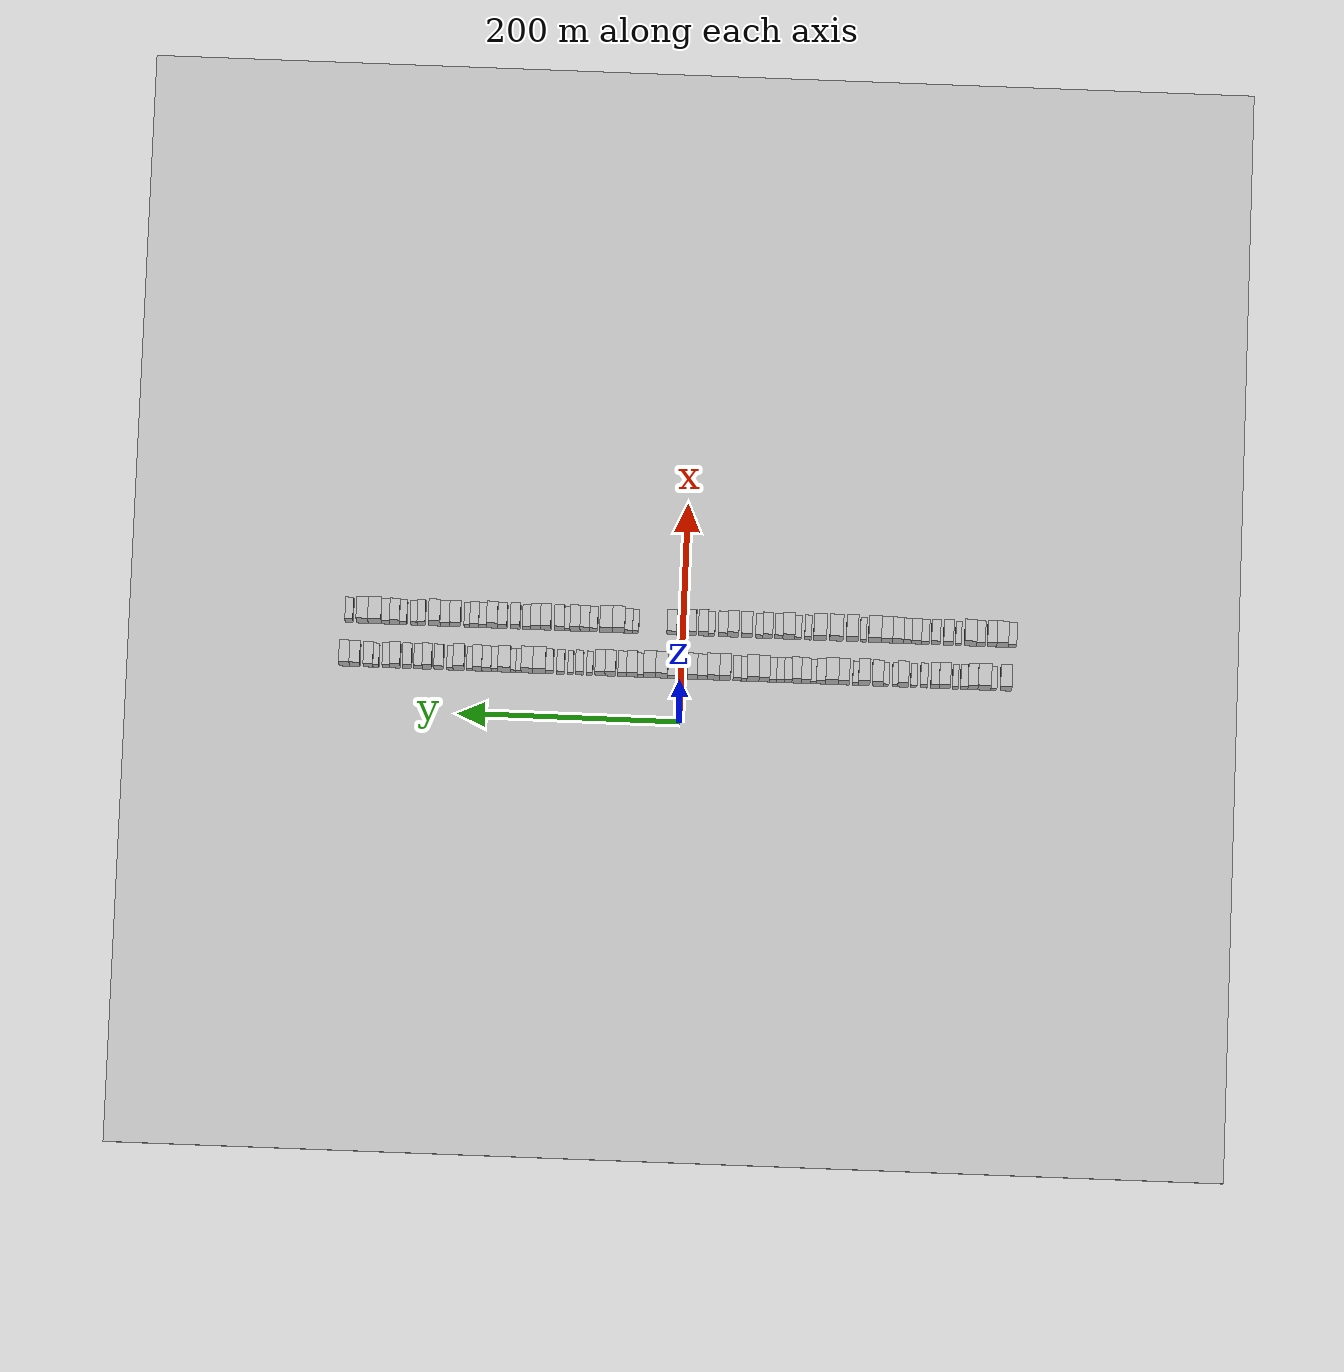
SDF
<?xml version="1.0" encoding="utf-8"?>

<sdf version="1.6">

   <world name="default">

      <gui fullscreen="0">

         <camera name="user_camera">

            <pose>-15 0 4.57585 0 0 0</pose>

            <view_controller>orbit</view_controller>

         </camera>

      </gui>

      <scene>

         <sky>

           <clouds>

             <speed>12</speed>

           </clouds>

         </sky>

         <ambient>0.4 0.4 0.4 1</ambient>

         <background>0.7 0.7 0.7 1</background>

         <shadows>1</shadows>

      </scene>

      <gravity>0 0 -9.8066</gravity>

      <magnetic_field>6e-06 2.3e-05 -4.2e-05</magnetic_field>

      <physics default="0" name="default_physics" type="ode">

         <ode>

            <solver>

               <type>quick</type>

               <iters>10</iters>

               <sor>1.0</sor>

               <use_dynamic_moi_rescaling>0</use_dynamic_moi_rescaling>

            </solver>

            <constraints>

               <cfm>0</cfm>

               <erp>0.2</erp>

               <contact_max_correcting_vel>100</contact_max_correcting_vel>

               <contact_surface_layer>0.001</contact_surface_layer>

            </constraints>

         </ode>

         <max_step_size>0.004</max_step_size>

         <real_time_factor>1</real_time_factor>

         <real_time_update_rate>250</real_time_update_rate>

      </physics>

      <light name="sun" type="directional">

         <cast_shadows>1</cast_shadows>

         <pose>0 0 10 0 0 0</pose>

         <diffuse>0.8 0.8 0.8 1</diffuse>

         <specular>0.2 0.2 0.2 1</specular>

         <attenuation>

            <range>1000</range>

            <constant>0.9</constant>

            <linear>0.01</linear>

            <quadratic>0.001</quadratic>

         </attenuation>

         <direction>-0.5 0.1 -0.9</direction>

      </light>

      <include>

         <name>ground_plane_1</name>

         <uri>model://HANNAS_ground_plane</uri>

         <pose>0 0 0  0 0 0</pose>

      </include>

      <include>

         <name>ground_plane_2</name>

         <uri>model://HANNAS_ground_plane</uri>

         <pose>100 0 0  0 0 0</pose>

      </include>

      <model name="building_1">

         <static>1</static>

         <pose frame="">50.0000 -291.7984 0 0.000000 0.000000 0.000000</pose>

         <link name="link">

            <pose frame="">0 0 10.50 0 0 0</pose>

            <collision name="collision">

               <geometry>

                  <box>

                     <size>20.0000 10.4033 21.0000</size>

                  </box>

               </geometry>

               <max_contacts>10</max_contacts>

               <surface>

                  <contact>

                     <ode/>

                  </contact>

                  <bounce/>

                  <friction>

                     <torsional>

                        <ode/>

                     </torsional>

                     <ode/>

                  </friction>

               </surface>

            </collision>

            <visual name="visual">

               <cast_shadows>0</cast_shadows>

               <geometry>

                  <box>

                     <size>20.0000 10.4033 21.0000</size>

                  </box>

               </geometry>

               <material>

                  <script>

                     <uri>model://HANNAS_wall/materials/scripts</uri>

                     <uri>model://HANNAS_wall/materials/textures</uri>

                     <name>vrc/HANNAS_wall</name>

                  </script>

               </material>

            </visual>

            <self_collide>0</self_collide>

            <enable_wind>0</enable_wind>

            <kinematic>0</kinematic>

         </link>

      </model>

      <model name="building_2">

         <static>1</static>

         <pose frame="">50.0000 -280.9232 0 0.000000 0.000000 0.000000</pose>

         <link name="link">

            <pose frame="">0 0 6.00 0 0 0</pose>

            <collision name="collision">

               <geometry>

                  <box>

                     <size>20.0000 5.3470 12.0000</size>

                  </box>

               </geometry>

               <max_contacts>10</max_contacts>

               <surface>

                  <contact>

                     <ode/>

                  </contact>

                  <bounce/>

                  <friction>

                     <torsional>

                        <ode/>

                     </torsional>

                     <ode/>

                  </friction>

               </surface>

            </collision>

            <visual name="visual">

               <cast_shadows>0</cast_shadows>

               <geometry>

                  <box>

                     <size>20.0000 5.3470 12.0000</size>

                  </box>

               </geometry>

               <material>

                  <script>

                     <uri>model://HANNAS_wall/materials/scripts</uri>

                     <uri>model://HANNAS_wall/materials/textures</uri>

                     <name>vrc/HANNAS_wall</name>

                  </script>

               </material>

            </visual>

            <self_collide>0</self_collide>

            <enable_wind>0</enable_wind>

            <kinematic>0</kinematic>

         </link>

      </model>

      <model name="building_3">

         <static>1</static>

         <pose frame="">50.0000 -272.3910 0 0.000000 0.000000 0.000000</pose>

         <link name="link">

            <pose frame="">0 0 12.00 0 0 0</pose>

            <collision name="collision">

               <geometry>

                  <box>

                     <size>20.0000 11.7176 24.0000</size>

                  </box>

               </geometry>

               <max_contacts>10</max_contacts>

               <surface>

                  <contact>

                     <ode/>

                  </contact>

                  <bounce/>

                  <friction>

                     <torsional>

                        <ode/>

                     </torsional>

                     <ode/>

                  </friction>

               </surface>

            </collision>

            <visual name="visual">

               <cast_shadows>0</cast_shadows>

               <geometry>

                  <box>

                     <size>20.0000 11.7176 24.0000</size>

                  </box>

               </geometry>

               <material>

                  <script>

                     <uri>model://HANNAS_wall/materials/scripts</uri>

                     <uri>model://HANNAS_wall/materials/textures</uri>

                     <name>vrc/HANNAS_wall</name>

                  </script>

               </material>

            </visual>

            <self_collide>0</self_collide>

            <enable_wind>0</enable_wind>

            <kinematic>0</kinematic>

         </link>

      </model>

      <model name="building_4">

         <static>1</static>

         <pose frame="">50.0000 -262.0434 0 0.000000 0.000000 0.000000</pose>

         <link name="link">

            <pose frame="">0 0 10.50 0 0 0</pose>

            <collision name="collision">

               <geometry>

                  <box>

                     <size>20.0000 8.9775 21.0000</size>

                  </box>

               </geometry>

               <max_contacts>10</max_contacts>

               <surface>

                  <contact>

                     <ode/>

                  </contact>

                  <bounce/>

                  <friction>

                     <torsional>

                        <ode/>

                     </torsional>

                     <ode/>

                  </friction>

               </surface>

            </collision>

            <visual name="visual">

               <cast_shadows>0</cast_shadows>

               <geometry>

                  <box>

                     <size>20.0000 8.9775 21.0000</size>

                  </box>

               </geometry>

               <material>

                  <script>

                     <uri>model://HANNAS_wall/materials/scripts</uri>

                     <uri>model://HANNAS_wall/materials/textures</uri>

                     <name>vrc/HANNAS_wall</name>

                  </script>

               </material>

            </visual>

            <self_collide>0</self_collide>

            <enable_wind>0</enable_wind>

            <kinematic>0</kinematic>

         </link>

      </model>

      <model name="building_5">

         <static>1</static>

         <pose frame="">50.0000 -254.2005 0 0.000000 0.000000 0.000000</pose>

         <link name="link">

            <pose frame="">0 0 7.50 0 0 0</pose>

            <collision name="collision">

               <geometry>

                  <box>

                     <size>20.0000 6.7083 15.0000</size>

                  </box>

               </geometry>

               <max_contacts>10</max_contacts>

               <surface>

                  <contact>

                     <ode/>

                  </contact>

                  <bounce/>

                  <friction>

                     <torsional>

                        <ode/>

                     </torsional>

                     <ode/>

                  </friction>

               </surface>

            </collision>

            <visual name="visual">

               <cast_shadows>0</cast_shadows>

               <geometry>

                  <box>

                     <size>20.0000 6.7083 15.0000</size>

                  </box>

               </geometry>

               <material>

                  <script>

                     <uri>model://HANNAS_wall/materials/scripts</uri>

                     <uri>model://HANNAS_wall/materials/textures</uri>

                     <name>vrc/HANNAS_wall</name>

                  </script>

               </material>

            </visual>

            <self_collide>0</self_collide>

            <enable_wind>0</enable_wind>

            <kinematic>0</kinematic>

         </link>

      </model>

      <model name="building_6">

         <static>1</static>

         <pose frame="">50.0000 -246.2385 0 0.000000 0.000000 0.000000</pose>

         <link name="link">

            <pose frame="">0 0 6.00 0 0 0</pose>

            <collision name="collision">

               <geometry>

                  <box>

                     <size>20.0000 5.2157 12.0000</size>

                  </box>

               </geometry>

               <max_contacts>10</max_contacts>

               <surface>

                  <contact>

                     <ode/>

                  </contact>

                  <bounce/>

                  <friction>

                     <torsional>

                        <ode/>

                     </torsional>

                     <ode/>

                  </friction>

               </surface>

            </collision>

            <visual name="visual">

               <cast_shadows>0</cast_shadows>

               <geometry>

                  <box>

                     <size>20.0000 5.2157 12.0000</size>

                  </box>

               </geometry>

               <material>

                  <script>

                     <uri>model://HANNAS_wall/materials/scripts</uri>

                     <uri>model://HANNAS_wall/materials/textures</uri>

                     <name>vrc/HANNAS_wall</name>

                  </script>

               </material>

            </visual>

            <self_collide>0</self_collide>

            <enable_wind>0</enable_wind>

            <kinematic>0</kinematic>

         </link>

      </model>

      <model name="building_7">

         <static>1</static>

         <pose frame="">50.0000 -236.6326 0 0.000000 0.000000 0.000000</pose>

         <link name="link">

            <pose frame="">0 0 10.50 0 0 0</pose>

            <collision name="collision">

               <geometry>

                  <box>

                     <size>20.0000 9.9960 21.0000</size>

                  </box>

               </geometry>

               <max_contacts>10</max_contacts>

               <surface>

                  <contact>

                     <ode/>

                  </contact>

                  <bounce/>

                  <friction>

                     <torsional>

                        <ode/>

                     </torsional>

                     <ode/>

                  </friction>

               </surface>

            </collision>

            <visual name="visual">

               <cast_shadows>0</cast_shadows>

               <geometry>

                  <box>

                     <size>20.0000 9.9960 21.0000</size>

                  </box>

               </geometry>

               <material>

                  <script>

                     <uri>model://HANNAS_wall/materials/scripts</uri>

                     <uri>model://HANNAS_wall/materials/textures</uri>

                     <name>vrc/HANNAS_wall</name>

                  </script>

               </material>

            </visual>

            <self_collide>0</self_collide>

            <enable_wind>0</enable_wind>

            <kinematic>0</kinematic>

         </link>

      </model>

      <model name="building_8">

         <static>1</static>

         <pose frame="">50.0000 -227.9022 0 0.000000 0.000000 0.000000</pose>

         <link name="link">

            <pose frame="">0 0 9.00 0 0 0</pose>

            <collision name="collision">

               <geometry>

                  <box>

                     <size>20.0000 7.4647 18.0000</size>

                  </box>

               </geometry>

               <max_contacts>10</max_contacts>

               <surface>

                  <contact>

                     <ode/>

                  </contact>

                  <bounce/>

                  <friction>

                     <torsional>

                        <ode/>

                     </torsional>

                     <ode/>

                  </friction>

               </surface>

            </collision>

            <visual name="visual">

               <cast_shadows>0</cast_shadows>

               <geometry>

                  <box>

                     <size>20.0000 7.4647 18.0000</size>

                  </box>

               </geometry>

               <material>

                  <script>

                     <uri>model://HANNAS_wall/materials/scripts</uri>

                     <uri>model://HANNAS_wall/materials/textures</uri>

                     <name>vrc/HANNAS_wall</name>

                  </script>

               </material>

            </visual>

            <self_collide>0</self_collide>

            <enable_wind>0</enable_wind>

            <kinematic>0</kinematic>

         </link>

      </model>

      <model name="building_9">

         <static>1</static>

         <pose frame="">50.0000 -217.9358 0 0.000000 0.000000 0.000000</pose>

         <link name="link">

            <pose frame="">0 0 7.50 0 0 0</pose>

            <collision name="collision">

               <geometry>

                  <box>

                     <size>20.0000 6.4683 15.0000</size>

                  </box>

               </geometry>

               <max_contacts>10</max_contacts>

               <surface>

                  <contact>

                     <ode/>

                  </contact>

                  <bounce/>

                  <friction>

                     <torsional>

                        <ode/>

                     </torsional>

                     <ode/>

                  </friction>

               </surface>

            </collision>

            <visual name="visual">

               <cast_shadows>0</cast_shadows>

               <geometry>

                  <box>

                     <size>20.0000 6.4683 15.0000</size>

                  </box>

               </geometry>

               <material>

                  <script>

                     <uri>model://HANNAS_wall/materials/scripts</uri>

                     <uri>model://HANNAS_wall/materials/textures</uri>

                     <name>vrc/HANNAS_wall</name>

                  </script>

               </material>

            </visual>

            <self_collide>0</self_collide>

            <enable_wind>0</enable_wind>

            <kinematic>0</kinematic>

         </link>

      </model>

      <model name="building_10">

         <static>1</static>

         <pose frame="">50.0000 -208.8359 0 0.000000 0.000000 0.000000</pose>

         <link name="link">

            <pose frame="">0 0 6.00 0 0 0</pose>

            <collision name="collision">

               <geometry>

                  <box>

                     <size>20.0000 5.7314 12.0000</size>

                  </box>

               </geometry>

               <max_contacts>10</max_contacts>

               <surface>

                  <contact>

                     <ode/>

                  </contact>

                  <bounce/>

                  <friction>

                     <torsional>

                        <ode/>

                     </torsional>

                     <ode/>

                  </friction>

               </surface>

            </collision>

            <visual name="visual">

               <cast_shadows>0</cast_shadows>

               <geometry>

                  <box>

                     <size>20.0000 5.7314 12.0000</size>

                  </box>

               </geometry>

               <material>

                  <script>

                     <uri>model://HANNAS_wall/materials/scripts</uri>

                     <uri>model://HANNAS_wall/materials/textures</uri>

                     <name>vrc/HANNAS_wall</name>

                  </script>

               </material>

            </visual>

            <self_collide>0</self_collide>

            <enable_wind>0</enable_wind>

            <kinematic>0</kinematic>

         </link>

      </model>

      <model name="building_11">

         <static>1</static>

         <pose frame="">50.0000 -199.2077 0 0.000000 0.000000 0.000000</pose>

         <link name="link">

            <pose frame="">0 0 10.50 0 0 0</pose>

            <collision name="collision">

               <geometry>

                  <box>

                     <size>20.0000 9.5249 21.0000</size>

                  </box>

               </geometry>

               <max_contacts>10</max_contacts>

               <surface>

                  <contact>

                     <ode/>

                  </contact>

                  <bounce/>

                  <friction>

                     <torsional>

                        <ode/>

                     </torsional>

                     <ode/>

                  </friction>

               </surface>

            </collision>

            <visual name="visual">

               <cast_shadows>0</cast_shadows>

               <geometry>

                  <box>

                     <size>20.0000 9.5249 21.0000</size>

                  </box>

               </geometry>

               <material>

                  <script>

                     <uri>model://HANNAS_wall/materials/scripts</uri>

                     <uri>model://HANNAS_wall/materials/textures</uri>

                     <name>vrc/HANNAS_wall</name>

                  </script>

               </material>

            </visual>

            <self_collide>0</self_collide>

            <enable_wind>0</enable_wind>

            <kinematic>0</kinematic>

         </link>

      </model>

      <model name="building_12">

         <static>1</static>

         <pose frame="">50.0000 -191.9415 0 0.000000 0.000000 0.000000</pose>

         <link name="link">

            <pose frame="">0 0 6.00 0 0 0</pose>

            <collision name="collision">

               <geometry>

                  <box>

                     <size>20.0000 5.0075 12.0000</size>

                  </box>

               </geometry>

               <max_contacts>10</max_contacts>

               <surface>

                  <contact>

                     <ode/>

                  </contact>

                  <bounce/>

                  <friction>

                     <torsional>

                        <ode/>

                     </torsional>

                     <ode/>

                  </friction>

               </surface>

            </collision>

            <visual name="visual">

               <cast_shadows>0</cast_shadows>

               <geometry>

                  <box>

                     <size>20.0000 5.0075 12.0000</size>

                  </box>

               </geometry>

               <material>

                  <script>

                     <uri>model://HANNAS_wall/materials/scripts</uri>

                     <uri>model://HANNAS_wall/materials/textures</uri>

                     <name>vrc/HANNAS_wall</name>

                  </script>

               </material>

            </visual>

            <self_collide>0</self_collide>

            <enable_wind>0</enable_wind>

            <kinematic>0</kinematic>

         </link>

      </model>

      <model name="building_13">

         <static>1</static>

         <pose frame="">50.0000 -183.9053 0 0.000000 0.000000 0.000000</pose>

         <link name="link">

            <pose frame="">0 0 6.00 0 0 0</pose>

            <collision name="collision">

               <geometry>

                  <box>

                     <size>20.0000 5.0648 12.0000</size>

                  </box>

               </geometry>

               <max_contacts>10</max_contacts>

               <surface>

                  <contact>

                     <ode/>

                  </contact>

                  <bounce/>

                  <friction>

                     <torsional>

                        <ode/>

                     </torsional>

                     <ode/>

                  </friction>

               </surface>

            </collision>

            <visual name="visual">

               <cast_shadows>0</cast_shadows>

               <geometry>

                  <box>

                     <size>20.0000 5.0648 12.0000</size>

                  </box>

               </geometry>

               <material>

                  <script>

                     <uri>model://HANNAS_wall/materials/scripts</uri>

                     <uri>model://HANNAS_wall/materials/textures</uri>

                     <name>vrc/HANNAS_wall</name>

                  </script>

               </material>

            </visual>

            <self_collide>0</self_collide>

            <enable_wind>0</enable_wind>

            <kinematic>0</kinematic>

         </link>

      </model>

      <model name="building_14">

         <static>1</static>

         <pose frame="">50.0000 -176.3470 0 0.000000 0.000000 0.000000</pose>

         <link name="link">

            <pose frame="">0 0 10.50 0 0 0</pose>

            <collision name="collision">

               <geometry>

                  <box>

                     <size>20.0000 10.0518 21.0000</size>

                  </box>

               </geometry>

               <max_contacts>10</max_contacts>

               <surface>

                  <contact>

                     <ode/>

                  </contact>

                  <bounce/>

                  <friction>

                     <torsional>

                        <ode/>

                     </torsional>

                     <ode/>

                  </friction>

               </surface>

            </collision>

            <visual name="visual">

               <cast_shadows>0</cast_shadows>

               <geometry>

                  <box>

                     <size>20.0000 10.0518 21.0000</size>

                  </box>

               </geometry>

               <material>

                  <script>

                     <uri>model://HANNAS_wall/materials/scripts</uri>

                     <uri>model://HANNAS_wall/materials/textures</uri>

                     <name>vrc/HANNAS_wall</name>

                  </script>

               </material>

            </visual>

            <self_collide>0</self_collide>

            <enable_wind>0</enable_wind>

            <kinematic>0</kinematic>

         </link>

      </model>

      <model name="building_15">

         <static>1</static>

         <pose frame="">50.0000 -164.1499 0 0.000000 0.000000 0.000000</pose>

         <link name="link">

            <pose frame="">0 0 12.00 0 0 0</pose>

            <collision name="collision">

               <geometry>

                  <box>

                     <size>20.0000 10.3426 24.0000</size>

                  </box>

               </geometry>

               <max_contacts>10</max_contacts>

               <surface>

                  <contact>

                     <ode/>

                  </contact>

                  <bounce/>

                  <friction>

                     <torsional>

                        <ode/>

                     </torsional>

                     <ode/>

                  </friction>

               </surface>

            </collision>

            <visual name="visual">

               <cast_shadows>0</cast_shadows>

               <geometry>

                  <box>

                     <size>20.0000 10.3426 24.0000</size>

                  </box>

               </geometry>

               <material>

                  <script>

                     <uri>model://HANNAS_wall/materials/scripts</uri>

                     <uri>model://HANNAS_wall/materials/textures</uri>

                     <name>vrc/HANNAS_wall</name>

                  </script>

               </material>

            </visual>

            <self_collide>0</self_collide>

            <enable_wind>0</enable_wind>

            <kinematic>0</kinematic>

         </link>

      </model>

      <model name="building_16">

         <static>1</static>

         <pose frame="">50.0000 -156.3811 0 0.000000 0.000000 0.000000</pose>

         <link name="link">

            <pose frame="">0 0 6.00 0 0 0</pose>

            <collision name="collision">

               <geometry>

                  <box>

                     <size>20.0000 5.1948 12.0000</size>

                  </box>

               </geometry>

               <max_contacts>10</max_contacts>

               <surface>

                  <contact>

                     <ode/>

                  </contact>

                  <bounce/>

                  <friction>

                     <torsional>

                        <ode/>

                     </torsional>

                     <ode/>

                  </friction>

               </surface>

            </collision>

            <visual name="visual">

               <cast_shadows>0</cast_shadows>

               <geometry>

                  <box>

                     <size>20.0000 5.1948 12.0000</size>

                  </box>

               </geometry>

               <material>

                  <script>

                     <uri>model://HANNAS_wall/materials/scripts</uri>

                     <uri>model://HANNAS_wall/materials/textures</uri>

                     <name>vrc/HANNAS_wall</name>

                  </script>

               </material>

            </visual>

            <self_collide>0</self_collide>

            <enable_wind>0</enable_wind>

            <kinematic>0</kinematic>

         </link>

      </model>

      <model name="building_17">

         <static>1</static>

         <pose frame="">50.0000 -145.9532 0 0.000000 0.000000 0.000000</pose>

         <link name="link">

            <pose frame="">0 0 10.50 0 0 0</pose>

            <collision name="collision">

               <geometry>

                  <box>

                     <size>20.0000 9.6611 21.0000</size>

                  </box>

               </geometry>

               <max_contacts>10</max_contacts>

               <surface>

                  <contact>

                     <ode/>

                  </contact>

                  <bounce/>

                  <friction>

                     <torsional>

                        <ode/>

                     </torsional>

                     <ode/>

                  </friction>

               </surface>

            </collision>

            <visual name="visual">

               <cast_shadows>0</cast_shadows>

               <geometry>

                  <box>

                     <size>20.0000 9.6611 21.0000</size>

                  </box>

               </geometry>

               <material>

                  <script>

                     <uri>model://HANNAS_wall/materials/scripts</uri>

                     <uri>model://HANNAS_wall/materials/textures</uri>

                     <name>vrc/HANNAS_wall</name>

                  </script>

               </material>

            </visual>

            <self_collide>0</self_collide>

            <enable_wind>0</enable_wind>

            <kinematic>0</kinematic>

         </link>

      </model>

      <model name="building_18">

         <static>1</static>

         <pose frame="">50.0000 -135.3062 0 0.000000 0.000000 0.000000</pose>

         <link name="link">

            <pose frame="">0 0 12.00 0 0 0</pose>

            <collision name="collision">

               <geometry>

                  <box>

                     <size>20.0000 11.6329 24.0000</size>

                  </box>

               </geometry>

               <max_contacts>10</max_contacts>

               <surface>

                  <contact>

                     <ode/>

                  </contact>

                  <bounce/>

                  <friction>

                     <torsional>

                        <ode/>

                     </torsional>

                     <ode/>

                  </friction>

               </surface>

            </collision>

            <visual name="visual">

               <cast_shadows>0</cast_shadows>

               <geometry>

                  <box>

                     <size>20.0000 11.6329 24.0000</size>

                  </box>

               </geometry>

               <material>

                  <script>

                     <uri>model://HANNAS_wall/materials/scripts</uri>

                     <uri>model://HANNAS_wall/materials/textures</uri>

                     <name>vrc/HANNAS_wall</name>

                  </script>

               </material>

            </visual>

            <self_collide>0</self_collide>

            <enable_wind>0</enable_wind>

            <kinematic>0</kinematic>

         </link>

      </model>

      <model name="building_19">

         <static>1</static>

         <pose frame="">50.0000 -125.2963 0 0.000000 0.000000 0.000000</pose>

         <link name="link">

            <pose frame="">0 0 9.00 0 0 0</pose>

            <collision name="collision">

               <geometry>

                  <box>

                     <size>20.0000 8.3871 18.0000</size>

                  </box>

               </geometry>

               <max_contacts>10</max_contacts>

               <surface>

                  <contact>

                     <ode/>

                  </contact>

                  <bounce/>

                  <friction>

                     <torsional>

                        <ode/>

                     </torsional>

                     <ode/>

                  </friction>

               </surface>

            </collision>

            <visual name="visual">

               <cast_shadows>0</cast_shadows>

               <geometry>

                  <box>

                     <size>20.0000 8.3871 18.0000</size>

                  </box>

               </geometry>

               <material>

                  <script>

                     <uri>model://HANNAS_wall/materials/scripts</uri>

                     <uri>model://HANNAS_wall/materials/textures</uri>

                     <name>vrc/HANNAS_wall</name>

                  </script>

               </material>

            </visual>

            <self_collide>0</self_collide>

            <enable_wind>0</enable_wind>

            <kinematic>0</kinematic>

         </link>

      </model>

      <model name="building_20">

         <static>1</static>

         <pose frame="">50.0000 -118.6462 0 0.000000 0.000000 0.000000</pose>

         <link name="link">

            <pose frame="">0 0 6.00 0 0 0</pose>

            <collision name="collision">

               <geometry>

                  <box>

                     <size>20.0000 4.9131 12.0000</size>

                  </box>

               </geometry>

               <max_contacts>10</max_contacts>

               <surface>

                  <contact>

                     <ode/>

                  </contact>

                  <bounce/>

                  <friction>

                     <torsional>

                        <ode/>

                     </torsional>

                     <ode/>

                  </friction>

               </surface>

            </collision>

            <visual name="visual">

               <cast_shadows>0</cast_shadows>

               <geometry>

                  <box>

                     <size>20.0000 4.9131 12.0000</size>

                  </box>

               </geometry>

               <material>

                  <script>

                     <uri>model://HANNAS_wall/materials/scripts</uri>

                     <uri>model://HANNAS_wall/materials/textures</uri>

                     <name>vrc/HANNAS_wall</name>

                  </script>

               </material>

            </visual>

            <self_collide>0</self_collide>

            <enable_wind>0</enable_wind>

            <kinematic>0</kinematic>

         </link>

      </model>

      <model name="building_21">

         <static>1</static>

         <pose frame="">50.0000 -111.9000 0 0.000000 0.000000 0.000000</pose>

         <link name="link">

            <pose frame="">0 0 9.00 0 0 0</pose>

            <collision name="collision">

               <geometry>

                  <box>

                     <size>20.0000 8.5792 18.0000</size>

                  </box>

               </geometry>

               <max_contacts>10</max_contacts>

               <surface>

                  <contact>

                     <ode/>

                  </contact>

                  <bounce/>

                  <friction>

                     <torsional>

                        <ode/>

                     </torsional>

                     <ode/>

                  </friction>

               </surface>

            </collision>

            <visual name="visual">

               <cast_shadows>0</cast_shadows>

               <geometry>

                  <box>

                     <size>20.0000 8.5792 18.0000</size>

                  </box>

               </geometry>

               <material>

                  <script>

                     <uri>model://HANNAS_wall/materials/scripts</uri>

                     <uri>model://HANNAS_wall/materials/textures</uri>

                     <name>vrc/HANNAS_wall</name>

                  </script>

               </material>

            </visual>

            <self_collide>0</self_collide>

            <enable_wind>0</enable_wind>

            <kinematic>0</kinematic>

         </link>

      </model>

      <model name="building_22">

         <static>1</static>

         <pose frame="">50.0000 -103.3777 0 0.000000 0.000000 0.000000</pose>

         <link name="link">

            <pose frame="">0 0 10.50 0 0 0</pose>

            <collision name="collision">

               <geometry>

                  <box>

                     <size>20.0000 8.4652 21.0000</size>

                  </box>

               </geometry>

               <max_contacts>10</max_contacts>

               <surface>

                  <contact>

                     <ode/>

                  </contact>

                  <bounce/>

                  <friction>

                     <torsional>

                        <ode/>

                     </torsional>

                     <ode/>

                  </friction>

               </surface>

            </collision>

            <visual name="visual">

               <cast_shadows>0</cast_shadows>

               <geometry>

                  <box>

                     <size>20.0000 8.4652 21.0000</size>

                  </box>

               </geometry>

               <material>

                  <script>

                     <uri>model://HANNAS_wall/materials/scripts</uri>

                     <uri>model://HANNAS_wall/materials/textures</uri>

                     <name>vrc/HANNAS_wall</name>

                  </script>

               </material>

            </visual>

            <self_collide>0</self_collide>

            <enable_wind>0</enable_wind>

            <kinematic>0</kinematic>

         </link>

      </model>

      <model name="building_23">

         <static>1</static>

         <pose frame="">50.0000 -95.6547 0 0.000000 0.000000 0.000000</pose>

         <link name="link">

            <pose frame="">0 0 7.50 0 0 0</pose>

            <collision name="collision">

               <geometry>

                  <box>

                     <size>20.0000 6.9809 15.0000</size>

                  </box>

               </geometry>

               <max_contacts>10</max_contacts>

               <surface>

                  <contact>

                     <ode/>

                  </contact>

                  <bounce/>

                  <friction>

                     <torsional>

                        <ode/>

                     </torsional>

                     <ode/>

                  </friction>

               </surface>

            </collision>

            <visual name="visual">

               <cast_shadows>0</cast_shadows>

               <geometry>

                  <box>

                     <size>20.0000 6.9809 15.0000</size>

                  </box>

               </geometry>

               <material>

                  <script>

                     <uri>model://HANNAS_wall/materials/scripts</uri>

                     <uri>model://HANNAS_wall/materials/textures</uri>

                     <name>vrc/HANNAS_wall</name>

                  </script>

               </material>

            </visual>

            <self_collide>0</self_collide>

            <enable_wind>0</enable_wind>

            <kinematic>0</kinematic>

         </link>

      </model>

      <model name="building_24">

         <static>1</static>

         <pose frame="">50.0000 -88.6900 0 0.000000 0.000000 0.000000</pose>

         <link name="link">

            <pose frame="">0 0 7.50 0 0 0</pose>

            <collision name="collision">

               <geometry>

                  <box>

                     <size>20.0000 6.9484 15.0000</size>

                  </box>

               </geometry>

               <max_contacts>10</max_contacts>

               <surface>

                  <contact>

                     <ode/>

                  </contact>

                  <bounce/>

                  <friction>

                     <torsional>

                        <ode/>

                     </torsional>

                     <ode/>

                  </friction>

               </surface>

            </collision>

            <visual name="visual">

               <cast_shadows>0</cast_shadows>

               <geometry>

                  <box>

                     <size>20.0000 6.9484 15.0000</size>

                  </box>

               </geometry>

               <material>

                  <script>

                     <uri>model://HANNAS_wall/materials/scripts</uri>

                     <uri>model://HANNAS_wall/materials/textures</uri>

                     <name>vrc/HANNAS_wall</name>

                  </script>

               </material>

            </visual>

            <self_collide>0</self_collide>

            <enable_wind>0</enable_wind>

            <kinematic>0</kinematic>

         </link>

      </model>

      <model name="building_25">

         <static>1</static>

         <pose frame="">50.0000 -82.2115 0 0.000000 0.000000 0.000000</pose>

         <link name="link">

            <pose frame="">0 0 7.50 0 0 0</pose>

            <collision name="collision">

               <geometry>

                  <box>

                     <size>20.0000 6.0088 15.0000</size>

                  </box>

               </geometry>

               <max_contacts>10</max_contacts>

               <surface>

                  <contact>

                     <ode/>

                  </contact>

                  <bounce/>

                  <friction>

                     <torsional>

                        <ode/>

                     </torsional>

                     <ode/>

                  </friction>

               </surface>

            </collision>

            <visual name="visual">

               <cast_shadows>0</cast_shadows>

               <geometry>

                  <box>

                     <size>20.0000 6.0088 15.0000</size>

                  </box>

               </geometry>

               <material>

                  <script>

                     <uri>model://HANNAS_wall/materials/scripts</uri>

                     <uri>model://HANNAS_wall/materials/textures</uri>

                     <name>vrc/HANNAS_wall</name>

                  </script>

               </material>

            </visual>

            <self_collide>0</self_collide>

            <enable_wind>0</enable_wind>

            <kinematic>0</kinematic>

         </link>

      </model>

      <model name="building_26">

         <static>1</static>

         <pose frame="">50.0000 -74.3394 0 0.000000 0.000000 0.000000</pose>

         <link name="link">

            <pose frame="">0 0 10.50 0 0 0</pose>

            <collision name="collision">

               <geometry>

                  <box>

                     <size>20.0000 9.7353 21.0000</size>

                  </box>

               </geometry>

               <max_contacts>10</max_contacts>

               <surface>

                  <contact>

                     <ode/>

                  </contact>

                  <bounce/>

                  <friction>

                     <torsional>

                        <ode/>

                     </torsional>

                     <ode/>

                  </friction>

               </surface>

            </collision>

            <visual name="visual">

               <cast_shadows>0</cast_shadows>

               <geometry>

                  <box>

                     <size>20.0000 9.7353 21.0000</size>

                  </box>

               </geometry>

               <material>

                  <script>

                     <uri>model://HANNAS_wall/materials/scripts</uri>

                     <uri>model://HANNAS_wall/materials/textures</uri>

                     <name>vrc/HANNAS_wall</name>

                  </script>

               </material>

            </visual>

            <self_collide>0</self_collide>

            <enable_wind>0</enable_wind>

            <kinematic>0</kinematic>

         </link>

      </model>

      <model name="building_27">

         <static>1</static>

         <pose frame="">50.0000 -64.0591 0 0.000000 0.000000 0.000000</pose>

         <link name="link">

            <pose frame="">0 0 12.00 0 0 0</pose>

            <collision name="collision">

               <geometry>

                  <box>

                     <size>20.0000 10.8253 24.0000</size>

                  </box>

               </geometry>

               <max_contacts>10</max_contacts>

               <surface>

                  <contact>

                     <ode/>

                  </contact>

                  <bounce/>

                  <friction>

                     <torsional>

                        <ode/>

                     </torsional>

                     <ode/>

                  </friction>

               </surface>

            </collision>

            <visual name="visual">

               <cast_shadows>0</cast_shadows>

               <geometry>

                  <box>

                     <size>20.0000 10.8253 24.0000</size>

                  </box>

               </geometry>

               <material>

                  <script>

                     <uri>model://HANNAS_wall/materials/scripts</uri>

                     <uri>model://HANNAS_wall/materials/textures</uri>

                     <name>vrc/HANNAS_wall</name>

                  </script>

               </material>

            </visual>

            <self_collide>0</self_collide>

            <enable_wind>0</enable_wind>

            <kinematic>0</kinematic>

         </link>

      </model>

      <model name="building_28">

         <static>1</static>

         <pose frame="">50.0000 -55.9848 0 0.000000 0.000000 0.000000</pose>

         <link name="link">

            <pose frame="">0 0 6.00 0 0 0</pose>

            <collision name="collision">

               <geometry>

                  <box>

                     <size>20.0000 5.3234 12.0000</size>

                  </box>

               </geometry>

               <max_contacts>10</max_contacts>

               <surface>

                  <contact>

                     <ode/>

                  </contact>

                  <bounce/>

                  <friction>

                     <torsional>

                        <ode/>

                     </torsional>

                     <ode/>

                  </friction>

               </surface>

            </collision>

            <visual name="visual">

               <cast_shadows>0</cast_shadows>

               <geometry>

                  <box>

                     <size>20.0000 5.3234 12.0000</size>

                  </box>

               </geometry>

               <material>

                  <script>

                     <uri>model://HANNAS_wall/materials/scripts</uri>

                     <uri>model://HANNAS_wall/materials/textures</uri>

                     <name>vrc/HANNAS_wall</name>

                  </script>

               </material>

            </visual>

            <self_collide>0</self_collide>

            <enable_wind>0</enable_wind>

            <kinematic>0</kinematic>

         </link>

      </model>

      <model name="building_29">

         <static>1</static>

         <pose frame="">50.0000 -49.6872 0 0.000000 0.000000 0.000000</pose>

         <link name="link">

            <pose frame="">0 0 9.00 0 0 0</pose>

            <collision name="collision">

               <geometry>

                  <box>

                     <size>20.0000 7.2717 18.0000</size>

                  </box>

               </geometry>

               <max_contacts>10</max_contacts>

               <surface>

                  <contact>

                     <ode/>

                  </contact>

                  <bounce/>

                  <friction>

                     <torsional>

                        <ode/>

                     </torsional>

                     <ode/>

                  </friction>

               </surface>

            </collision>

            <visual name="visual">

               <cast_shadows>0</cast_shadows>

               <geometry>

                  <box>

                     <size>20.0000 7.2717 18.0000</size>

                  </box>

               </geometry>

               <material>

                  <script>

                     <uri>model://HANNAS_wall/materials/scripts</uri>

                     <uri>model://HANNAS_wall/materials/textures</uri>

                     <name>vrc/HANNAS_wall</name>

                  </script>

               </material>

            </visual>

            <self_collide>0</self_collide>

            <enable_wind>0</enable_wind>

            <kinematic>0</kinematic>

         </link>

      </model>

      <model name="building_30">

         <static>1</static>

         <pose frame="">50.0000 -39.0021 0 0.000000 0.000000 0.000000</pose>

         <link name="link">

            <pose frame="">0 0 12.00 0 0 0</pose>

            <collision name="collision">

               <geometry>

                  <box>

                     <size>20.0000 10.0985 24.0000</size>

                  </box>

               </geometry>

               <max_contacts>10</max_contacts>

               <surface>

                  <contact>

                     <ode/>

                  </contact>

                  <bounce/>

                  <friction>

                     <torsional>

                        <ode/>

                     </torsional>

                     <ode/>

                  </friction>

               </surface>

            </collision>

            <visual name="visual">

               <cast_shadows>0</cast_shadows>

               <geometry>

                  <box>

                     <size>20.0000 10.0985 24.0000</size>

                  </box>

               </geometry>

               <material>

                  <script>

                     <uri>model://HANNAS_wall/materials/scripts</uri>

                     <uri>model://HANNAS_wall/materials/textures</uri>

                     <name>vrc/HANNAS_wall</name>

                  </script>

               </material>

            </visual>

            <self_collide>0</self_collide>

            <enable_wind>0</enable_wind>

            <kinematic>0</kinematic>

         </link>

      </model>

      <model name="building_31">

         <static>1</static>

         <pose frame="">50.0000 -28.3409 0 0.000000 0.000000 0.000000</pose>

         <link name="link">

            <pose frame="">0 0 12.00 0 0 0</pose>

            <collision name="collision">

               <geometry>

                  <box>

                     <size>20.0000 11.2239 24.0000</size>

                  </box>

               </geometry>

               <max_contacts>10</max_contacts>

               <surface>

                  <contact>

                     <ode/>

                  </contact>

                  <bounce/>

                  <friction>

                     <torsional>

                        <ode/>

                     </torsional>

                     <ode/>

                  </friction>

               </surface>

            </collision>

            <visual name="visual">

               <cast_shadows>0</cast_shadows>

               <geometry>

                  <box>

                     <size>20.0000 11.2239 24.0000</size>

                  </box>

               </geometry>

               <material>

                  <script>

                     <uri>model://HANNAS_wall/materials/scripts</uri>

                     <uri>model://HANNAS_wall/materials/textures</uri>

                     <name>vrc/HANNAS_wall</name>

                  </script>

               </material>

            </visual>

            <self_collide>0</self_collide>

            <enable_wind>0</enable_wind>

            <kinematic>0</kinematic>

         </link>

      </model>

      <model name="building_32">

         <static>1</static>

         <pose frame="">50.0000 -18.3390 0 0.000000 0.000000 0.000000</pose>

         <link name="link">

            <pose frame="">0 0 9.00 0 0 0</pose>

            <collision name="collision">

               <geometry>

                  <box>

                     <size>20.0000 8.7800 18.0000</size>

                  </box>

               </geometry>

               <max_contacts>10</max_contacts>

               <surface>

                  <contact>

                     <ode/>

                  </contact>

                  <bounce/>

                  <friction>

                     <torsional>

                        <ode/>

                     </torsional>

                     <ode/>

                  </friction>

               </surface>

            </collision>

            <visual name="visual">

               <cast_shadows>0</cast_shadows>

               <geometry>

                  <box>

                     <size>20.0000 8.7800 18.0000</size>

                  </box>

               </geometry>

               <material>

                  <script>

                     <uri>model://HANNAS_wall/materials/scripts</uri>

                     <uri>model://HANNAS_wall/materials/textures</uri>

                     <name>vrc/HANNAS_wall</name>

                  </script>

               </material>

            </visual>

            <self_collide>0</self_collide>

            <enable_wind>0</enable_wind>

            <kinematic>0</kinematic>

         </link>

      </model>

      <model name="building_33">

         <static>1</static>

         <pose frame="">50.0000 -9.5903 0 0.000000 0.000000 0.000000</pose>

         <link name="link">

            <pose frame="">0 0 10.50 0 0 0</pose>

            <collision name="collision">

               <geometry>

                  <box>

                     <size>20.0000 8.7173 21.0000</size>

                  </box>

               </geometry>

               <max_contacts>10</max_contacts>

               <surface>

                  <contact>

                     <ode/>

                  </contact>

                  <bounce/>

                  <friction>

                     <torsional>

                        <ode/>

                     </torsional>

                     <ode/>

                  </friction>

               </surface>

            </collision>

            <visual name="visual">

               <cast_shadows>0</cast_shadows>

               <geometry>

                  <box>

                     <size>20.0000 8.7173 21.0000</size>

                  </box>

               </geometry>

               <material>

                  <script>

                     <uri>model://HANNAS_wall/materials/scripts</uri>

                     <uri>model://HANNAS_wall/materials/textures</uri>

                     <name>vrc/HANNAS_wall</name>

                  </script>

               </material>

            </visual>

            <self_collide>0</self_collide>

            <enable_wind>0</enable_wind>

            <kinematic>0</kinematic>

         </link>

      </model>

      <model name="building_34">

         <static>1</static>

         <pose frame="">50.0000 0.0776 0 0.000000 0.000000 0.000000</pose>

         <link name="link">

            <pose frame="">0 0 12.00 0 0 0</pose>

            <collision name="collision">

               <geometry>

                  <box>

                     <size>20.0000 10.6185 24.0000</size>

                  </box>

               </geometry>

               <max_contacts>10</max_contacts>

               <surface>

                  <contact>

                     <ode/>

                  </contact>

                  <bounce/>

                  <friction>

                     <torsional>

                        <ode/>

                     </torsional>

                     <ode/>

                  </friction>

               </surface>

            </collision>

            <visual name="visual">

               <cast_shadows>0</cast_shadows>

               <geometry>

                  <box>

                     <size>20.0000 10.6185 24.0000</size>

                  </box>

               </geometry>

               <material>

                  <script>

                     <uri>model://HANNAS_wall/materials/scripts</uri>

                     <uri>model://HANNAS_wall/materials/textures</uri>

                     <name>vrc/HANNAS_wall</name>

                  </script>

               </material>

            </visual>

            <self_collide>0</self_collide>

            <enable_wind>0</enable_wind>

            <kinematic>0</kinematic>

         </link>

      </model>

      <model name="building_35">

         <static>1</static>

         <pose frame="">50.0000 8.9988 0 0.000000 0.000000 0.000000</pose>

         <link name="link">

            <pose frame="">0 0 7.50 0 0 0</pose>

            <collision name="collision">

               <geometry>

                  <box>

                     <size>20.0000 7.2240 15.0000</size>

                  </box>

               </geometry>

               <max_contacts>10</max_contacts>

               <surface>

                  <contact>

                     <ode/>

                  </contact>

                  <bounce/>

                  <friction>

                     <torsional>

                        <ode/>

                     </torsional>

                     <ode/>

                  </friction>

               </surface>

            </collision>

            <visual name="visual">

               <cast_shadows>0</cast_shadows>

               <geometry>

                  <box>

                     <size>20.0000 7.2240 15.0000</size>

                  </box>

               </geometry>

               <material>

                  <script>

                     <uri>model://HANNAS_wall/materials/scripts</uri>

                     <uri>model://HANNAS_wall/materials/textures</uri>

                     <name>vrc/HANNAS_wall</name>

                  </script>

               </material>

            </visual>

            <self_collide>0</self_collide>

            <enable_wind>0</enable_wind>

            <kinematic>0</kinematic>

         </link>

      </model>

      <model name="building_36">

         <static>1</static>

         <pose frame="">50.0000 18.1661 0 0.000000 0.000000 0.000000</pose>

         <link name="link">

            <pose frame="">0 0 12.00 0 0 0</pose>

            <collision name="collision">

               <geometry>

                  <box>

                     <size>20.0000 11.1104 24.0000</size>

                  </box>

               </geometry>

               <max_contacts>10</max_contacts>

               <surface>

                  <contact>

                     <ode/>

                  </contact>

                  <bounce/>

                  <friction>

                     <torsional>

                        <ode/>

                     </torsional>

                     <ode/>

                  </friction>

               </surface>

            </collision>

            <visual name="visual">

               <cast_shadows>0</cast_shadows>

               <geometry>

                  <box>

                     <size>20.0000 11.1104 24.0000</size>

                  </box>

               </geometry>

               <material>

                  <script>

                     <uri>model://HANNAS_wall/materials/scripts</uri>

                     <uri>model://HANNAS_wall/materials/textures</uri>

                     <name>vrc/HANNAS_wall</name>

                  </script>

               </material>

            </visual>

            <self_collide>0</self_collide>

            <enable_wind>0</enable_wind>

            <kinematic>0</kinematic>

         </link>

      </model>

      <model name="building_37">

         <static>1</static>

         <pose frame="">50.0000 29.1896 0 0.000000 0.000000 0.000000</pose>

         <link name="link">

            <pose frame="">0 0 12.00 0 0 0</pose>

            <collision name="collision">

               <geometry>

                  <box>

                     <size>20.0000 10.9366 24.0000</size>

                  </box>

               </geometry>

               <max_contacts>10</max_contacts>

               <surface>

                  <contact>

                     <ode/>

                  </contact>

                  <bounce/>

                  <friction>

                     <torsional>

                        <ode/>

                     </torsional>

                     <ode/>

                  </friction>

               </surface>

            </collision>

            <visual name="visual">

               <cast_shadows>0</cast_shadows>

               <geometry>

                  <box>

                     <size>20.0000 10.9366 24.0000</size>

                  </box>

               </geometry>

               <material>

                  <script>

                     <uri>model://HANNAS_wall/materials/scripts</uri>

                     <uri>model://HANNAS_wall/materials/textures</uri>

                     <name>vrc/HANNAS_wall</name>

                  </script>

               </material>

            </visual>

            <self_collide>0</self_collide>

            <enable_wind>0</enable_wind>

            <kinematic>0</kinematic>

         </link>

      </model>

      <model name="building_38">

         <static>1</static>

         <pose frame="">50.0000 37.4352 0 0.000000 0.000000 0.000000</pose>

         <link name="link">

            <pose frame="">0 0 6.00 0 0 0</pose>

            <collision name="collision">

               <geometry>

                  <box>

                     <size>20.0000 5.5546 12.0000</size>

                  </box>

               </geometry>

               <max_contacts>10</max_contacts>

               <surface>

                  <contact>

                     <ode/>

                  </contact>

                  <bounce/>

                  <friction>

                     <torsional>

                        <ode/>

                     </torsional>

                     <ode/>

                  </friction>

               </surface>

            </collision>

            <visual name="visual">

               <cast_shadows>0</cast_shadows>

               <geometry>

                  <box>

                     <size>20.0000 5.5546 12.0000</size>

                  </box>

               </geometry>

               <material>

                  <script>

                     <uri>model://HANNAS_wall/materials/scripts</uri>

                     <uri>model://HANNAS_wall/materials/textures</uri>

                     <name>vrc/HANNAS_wall</name>

                  </script>

               </material>

            </visual>

            <self_collide>0</self_collide>

            <enable_wind>0</enable_wind>

            <kinematic>0</kinematic>

         </link>

      </model>

      <model name="building_39">

         <static>1</static>

         <pose frame="">50.0000 45.0216 0 0.000000 0.000000 0.000000</pose>

         <link name="link">

            <pose frame="">0 0 10.50 0 0 0</pose>

            <collision name="collision">

               <geometry>

                  <box>

                     <size>20.0000 9.6183 21.0000</size>

                  </box>

               </geometry>

               <max_contacts>10</max_contacts>

               <surface>

                  <contact>

                     <ode/>

                  </contact>

                  <bounce/>

                  <friction>

                     <torsional>

                        <ode/>

                     </torsional>

                     <ode/>

                  </friction>

               </surface>

            </collision>

            <visual name="visual">

               <cast_shadows>0</cast_shadows>

               <geometry>

                  <box>

                     <size>20.0000 9.6183 21.0000</size>

                  </box>

               </geometry>

               <material>

                  <script>

                     <uri>model://HANNAS_wall/materials/scripts</uri>

                     <uri>model://HANNAS_wall/materials/textures</uri>

                     <name>vrc/HANNAS_wall</name>

                  </script>

               </material>

            </visual>

            <self_collide>0</self_collide>

            <enable_wind>0</enable_wind>

            <kinematic>0</kinematic>

         </link>

      </model>

      <model name="building_40">

         <static>1</static>

         <pose frame="">50.0000 53.6917 0 0.000000 0.000000 0.000000</pose>

         <link name="link">

            <pose frame="">0 0 9.00 0 0 0</pose>

            <collision name="collision">

               <geometry>

                  <box>

                     <size>20.0000 7.7219 18.0000</size>

                  </box>

               </geometry>

               <max_contacts>10</max_contacts>

               <surface>

                  <contact>

                     <ode/>

                  </contact>

                  <bounce/>

                  <friction>

                     <torsional>

                        <ode/>

                     </torsional>

                     <ode/>

                  </friction>

               </surface>

            </collision>

            <visual name="visual">

               <cast_shadows>0</cast_shadows>

               <geometry>

                  <box>

                     <size>20.0000 7.7219 18.0000</size>

                  </box>

               </geometry>

               <material>

                  <script>

                     <uri>model://HANNAS_wall/materials/scripts</uri>

                     <uri>model://HANNAS_wall/materials/textures</uri>

                     <name>vrc/HANNAS_wall</name>

                  </script>

               </material>

            </visual>

            <self_collide>0</self_collide>

            <enable_wind>0</enable_wind>

            <kinematic>0</kinematic>

         </link>

      </model>

      <model name="building_41">

         <static>1</static>

         <pose frame="">50.0000 64.3561 0 0.000000 0.000000 0.000000</pose>

         <link name="link">

            <pose frame="">0 0 10.50 0 0 0</pose>

            <collision name="collision">

               <geometry>

                  <box>

                     <size>20.0000 9.6068 21.0000</size>

                  </box>

               </geometry>

               <max_contacts>10</max_contacts>

               <surface>

                  <contact>

                     <ode/>

                  </contact>

                  <bounce/>

                  <friction>

                     <torsional>

                        <ode/>

                     </torsional>

                     <ode/>

                  </friction>

               </surface>

            </collision>

            <visual name="visual">

               <cast_shadows>0</cast_shadows>

               <geometry>

                  <box>

                     <size>20.0000 9.6068 21.0000</size>

                  </box>

               </geometry>

               <material>

                  <script>

                     <uri>model://HANNAS_wall/materials/scripts</uri>

                     <uri>model://HANNAS_wall/materials/textures</uri>

                     <name>vrc/HANNAS_wall</name>

                  </script>

               </material>

            </visual>

            <self_collide>0</self_collide>

            <enable_wind>0</enable_wind>

            <kinematic>0</kinematic>

         </link>

      </model>

      <model name="building_42">

         <static>1</static>

         <pose frame="">50.0000 73.6886 0 0.000000 0.000000 0.000000</pose>

         <link name="link">

            <pose frame="">0 0 10.50 0 0 0</pose>

            <collision name="collision">

               <geometry>

                  <box>

                     <size>20.0000 9.0583 21.0000</size>

                  </box>

               </geometry>

               <max_contacts>10</max_contacts>

               <surface>

                  <contact>

                     <ode/>

                  </contact>

                  <bounce/>

                  <friction>

                     <torsional>

                        <ode/>

                     </torsional>

                     <ode/>

                  </friction>

               </surface>

            </collision>

            <visual name="visual">

               <cast_shadows>0</cast_shadows>

               <geometry>

                  <box>

                     <size>20.0000 9.0583 21.0000</size>

                  </box>

               </geometry>

               <material>

                  <script>

                     <uri>model://HANNAS_wall/materials/scripts</uri>

                     <uri>model://HANNAS_wall/materials/textures</uri>

                     <name>vrc/HANNAS_wall</name>

                  </script>

               </material>

            </visual>

            <self_collide>0</self_collide>

            <enable_wind>0</enable_wind>

            <kinematic>0</kinematic>

         </link>

      </model>

      <model name="building_43">

         <static>1</static>

         <pose frame="">50.0000 83.0665 0 0.000000 0.000000 0.000000</pose>

         <link name="link">

            <pose frame="">0 0 6.00 0 0 0</pose>

            <collision name="collision">

               <geometry>

                  <box>

                     <size>20.0000 5.6975 12.0000</size>

                  </box>

               </geometry>

               <max_contacts>10</max_contacts>

               <surface>

                  <contact>

                     <ode/>

                  </contact>

                  <bounce/>

                  <friction>

                     <torsional>

                        <ode/>

                     </torsional>

                     <ode/>

                  </friction>

               </surface>

            </collision>

            <visual name="visual">

               <cast_shadows>0</cast_shadows>

               <geometry>

                  <box>

                     <size>20.0000 5.6975 12.0000</size>

                  </box>

               </geometry>

               <material>

                  <script>

                     <uri>model://HANNAS_wall/materials/scripts</uri>

                     <uri>model://HANNAS_wall/materials/textures</uri>

                     <name>vrc/HANNAS_wall</name>

                  </script>

               </material>

            </visual>

            <self_collide>0</self_collide>

            <enable_wind>0</enable_wind>

            <kinematic>0</kinematic>

         </link>

      </model>

      <model name="building_44">

         <static>1</static>

         <pose frame="">50.0000 92.3991 0 0.000000 0.000000 0.000000</pose>

         <link name="link">

            <pose frame="">0 0 7.50 0 0 0</pose>

            <collision name="collision">

               <geometry>

                  <box>

                     <size>20.0000 6.9675 15.0000</size>

                  </box>

               </geometry>

               <max_contacts>10</max_contacts>

               <surface>

                  <contact>

                     <ode/>

                  </contact>

                  <bounce/>

                  <friction>

                     <torsional>

                        <ode/>

                     </torsional>

                     <ode/>

                  </friction>

               </surface>

            </collision>

            <visual name="visual">

               <cast_shadows>0</cast_shadows>

               <geometry>

                  <box>

                     <size>20.0000 6.9675 15.0000</size>

                  </box>

               </geometry>

               <material>

                  <script>

                     <uri>model://HANNAS_wall/materials/scripts</uri>

                     <uri>model://HANNAS_wall/materials/textures</uri>

                     <name>vrc/HANNAS_wall</name>

                  </script>

               </material>

            </visual>

            <self_collide>0</self_collide>

            <enable_wind>0</enable_wind>

            <kinematic>0</kinematic>

         </link>

      </model>

      <model name="building_45">

         <static>1</static>

         <pose frame="">50.0000 100.3335 0 0.000000 0.000000 0.000000</pose>

         <link name="link">

            <pose frame="">0 0 6.00 0 0 0</pose>

            <collision name="collision">

               <geometry>

                  <box>

                     <size>20.0000 4.9013 12.0000</size>

                  </box>

               </geometry>

               <max_contacts>10</max_contacts>

               <surface>

                  <contact>

                     <ode/>

                  </contact>

                  <bounce/>

                  <friction>

                     <torsional>

                        <ode/>

                     </torsional>

                     <ode/>

                  </friction>

               </surface>

            </collision>

            <visual name="visual">

               <cast_shadows>0</cast_shadows>

               <geometry>

                  <box>

                     <size>20.0000 4.9013 12.0000</size>

                  </box>

               </geometry>

               <material>

                  <script>

                     <uri>model://HANNAS_wall/materials/scripts</uri>

                     <uri>model://HANNAS_wall/materials/textures</uri>

                     <name>vrc/HANNAS_wall</name>

                  </script>

               </material>

            </visual>

            <self_collide>0</self_collide>

            <enable_wind>0</enable_wind>

            <kinematic>0</kinematic>

         </link>

      </model>

      <model name="building_46">

         <static>1</static>

         <pose frame="">50.0000 109.2927 0 0.000000 0.000000 0.000000</pose>

         <link name="link">

            <pose frame="">0 0 7.50 0 0 0</pose>

            <collision name="collision">

               <geometry>

                  <box>

                     <size>20.0000 7.0171 15.0000</size>

                  </box>

               </geometry>

               <max_contacts>10</max_contacts>

               <surface>

                  <contact>

                     <ode/>

                  </contact>

                  <bounce/>

                  <friction>

                     <torsional>

                        <ode/>

                     </torsional>

                     <ode/>

                  </friction>

               </surface>

            </collision>

            <visual name="visual">

               <cast_shadows>0</cast_shadows>

               <geometry>

                  <box>

                     <size>20.0000 7.0171 15.0000</size>

                  </box>

               </geometry>

               <material>

                  <script>

                     <uri>model://HANNAS_wall/materials/scripts</uri>

                     <uri>model://HANNAS_wall/materials/textures</uri>

                     <name>vrc/HANNAS_wall</name>

                  </script>

               </material>

            </visual>

            <self_collide>0</self_collide>

            <enable_wind>0</enable_wind>

            <kinematic>0</kinematic>

         </link>

      </model>

      <model name="building_47">

         <static>1</static>

         <pose frame="">50.0000 119.2499 0 0.000000 0.000000 0.000000</pose>

         <link name="link">

            <pose frame="">0 0 7.50 0 0 0</pose>

            <collision name="collision">

               <geometry>

                  <box>

                     <size>20.0000 6.8973 15.0000</size>

                  </box>

               </geometry>

               <max_contacts>10</max_contacts>

               <surface>

                  <contact>

                     <ode/>

                  </contact>

                  <bounce/>

                  <friction>

                     <torsional>

                        <ode/>

                     </torsional>

                     <ode/>

                  </friction>

               </surface>

            </collision>

            <visual name="visual">

               <cast_shadows>0</cast_shadows>

               <geometry>

                  <box>

                     <size>20.0000 6.8973 15.0000</size>

                  </box>

               </geometry>

               <material>

                  <script>

                     <uri>model://HANNAS_wall/materials/scripts</uri>

                     <uri>model://HANNAS_wall/materials/textures</uri>

                     <name>vrc/HANNAS_wall</name>

                  </script>

               </material>

            </visual>

            <self_collide>0</self_collide>

            <enable_wind>0</enable_wind>

            <kinematic>0</kinematic>

         </link>

      </model>

      <model name="building_48">

         <static>1</static>

         <pose frame="">50.0000 128.4624 0 0.000000 0.000000 0.000000</pose>

         <link name="link">

            <pose frame="">0 0 12.00 0 0 0</pose>

            <collision name="collision">

               <geometry>

                  <box>

                     <size>20.0000 11.5277 24.0000</size>

                  </box>

               </geometry>

               <max_contacts>10</max_contacts>

               <surface>

                  <contact>

                     <ode/>

                  </contact>

                  <bounce/>

                  <friction>

                     <torsional>

                        <ode/>

                     </torsional>

                     <ode/>

                  </friction>

               </surface>

            </collision>

            <visual name="visual">

               <cast_shadows>0</cast_shadows>

               <geometry>

                  <box>

                     <size>20.0000 11.5277 24.0000</size>

                  </box>

               </geometry>

               <material>

                  <script>

                     <uri>model://HANNAS_wall/materials/scripts</uri>

                     <uri>model://HANNAS_wall/materials/textures</uri>

                     <name>vrc/HANNAS_wall</name>

                  </script>

               </material>

            </visual>

            <self_collide>0</self_collide>

            <enable_wind>0</enable_wind>

            <kinematic>0</kinematic>

         </link>

      </model>

      <model name="building_49">

         <static>1</static>

         <pose frame="">50.0000 139.4793 0 0.000000 0.000000 0.000000</pose>

         <link name="link">

            <pose frame="">0 0 12.00 0 0 0</pose>

            <collision name="collision">

               <geometry>

                  <box>

                     <size>20.0000 10.5061 24.0000</size>

                  </box>

               </geometry>

               <max_contacts>10</max_contacts>

               <surface>

                  <contact>

                     <ode/>

                  </contact>

                  <bounce/>

                  <friction>

                     <torsional>

                        <ode/>

                     </torsional>

                     <ode/>

                  </friction>

               </surface>

            </collision>

            <visual name="visual">

               <cast_shadows>0</cast_shadows>

               <geometry>

                  <box>

                     <size>20.0000 10.5061 24.0000</size>

                  </box>

               </geometry>

               <material>

                  <script>

                     <uri>model://HANNAS_wall/materials/scripts</uri>

                     <uri>model://HANNAS_wall/materials/textures</uri>

                     <name>vrc/HANNAS_wall</name>

                  </script>

               </material>

            </visual>

            <self_collide>0</self_collide>

            <enable_wind>0</enable_wind>

            <kinematic>0</kinematic>

         </link>

      </model>

      <model name="building_50">

         <static>1</static>

         <pose frame="">50.0000 147.1535 0 0.000000 0.000000 0.000000</pose>

         <link name="link">

            <pose frame="">0 0 6.00 0 0 0</pose>

            <collision name="collision">

               <geometry>

                  <box>

                     <size>20.0000 4.8423 12.0000</size>

                  </box>

               </geometry>

               <max_contacts>10</max_contacts>

               <surface>

                  <contact>

                     <ode/>

                  </contact>

                  <bounce/>

                  <friction>

                     <torsional>

                        <ode/>

                     </torsional>

                     <ode/>

                  </friction>

               </surface>

            </collision>

            <visual name="visual">

               <cast_shadows>0</cast_shadows>

               <geometry>

                  <box>

                     <size>20.0000 4.8423 12.0000</size>

                  </box>

               </geometry>

               <material>

                  <script>

                     <uri>model://HANNAS_wall/materials/scripts</uri>

                     <uri>model://HANNAS_wall/materials/textures</uri>

                     <name>vrc/HANNAS_wall</name>

                  </script>

               </material>

            </visual>

            <self_collide>0</self_collide>

            <enable_wind>0</enable_wind>

            <kinematic>0</kinematic>

         </link>

      </model>

      <model name="building_51">

         <static>1</static>

         <pose frame="">50.0000 152.0326 0 0.000000 0.000000 0.000000</pose>

         <link name="link">

            <pose frame="">0 0 6.00 0 0 0</pose>

            <collision name="collision">

               <geometry>

                  <box>

                     <size>20.0000 4.9160 12.0000</size>

                  </box>

               </geometry>

               <max_contacts>10</max_contacts>

               <surface>

                  <contact>

                     <ode/>

                  </contact>

                  <bounce/>

                  <friction>

                     <torsional>

                        <ode/>

                     </torsional>

                     <ode/>

                  </friction>

               </surface>

            </collision>

            <visual name="visual">

               <cast_shadows>0</cast_shadows>

               <geometry>

                  <box>

                     <size>20.0000 4.9160 12.0000</size>

                  </box>

               </geometry>

               <material>

                  <script>

                     <uri>model://HANNAS_wall/materials/scripts</uri>

                     <uri>model://HANNAS_wall/materials/textures</uri>

                     <name>vrc/HANNAS_wall</name>

                  </script>

               </material>

            </visual>

            <self_collide>0</self_collide>

            <enable_wind>0</enable_wind>

            <kinematic>0</kinematic>

         </link>

      </model>

      <model name="building_52">

         <static>1</static>

         <pose frame="">50.0000 160.0803 0 0.000000 0.000000 0.000000</pose>

         <link name="link">

            <pose frame="">0 0 12.00 0 0 0</pose>

            <collision name="collision">

               <geometry>

                  <box>

                     <size>20.0000 11.1795 24.0000</size>

                  </box>

               </geometry>

               <max_contacts>10</max_contacts>

               <surface>

                  <contact>

                     <ode/>

                  </contact>

                  <bounce/>

                  <friction>

                     <torsional>

                        <ode/>

                     </torsional>

                     <ode/>

                  </friction>

               </surface>

            </collision>

            <visual name="visual">

               <cast_shadows>0</cast_shadows>

               <geometry>

                  <box>

                     <size>20.0000 11.1795 24.0000</size>

                  </box>

               </geometry>

               <material>

                  <script>

                     <uri>model://HANNAS_wall/materials/scripts</uri>

                     <uri>model://HANNAS_wall/materials/textures</uri>

                     <name>vrc/HANNAS_wall</name>

                  </script>

               </material>

            </visual>

            <self_collide>0</self_collide>

            <enable_wind>0</enable_wind>

            <kinematic>0</kinematic>

         </link>

      </model>

      <model name="building_53">

         <static>1</static>

         <pose frame="">50.0000 168.6992 0 0.000000 0.000000 0.000000</pose>

         <link name="link">

            <pose frame="">0 0 7.50 0 0 0</pose>

            <collision name="collision">

               <geometry>

                  <box>

                     <size>20.0000 6.0583 15.0000</size>

                  </box>

               </geometry>

               <max_contacts>10</max_contacts>

               <surface>

                  <contact>

                     <ode/>

                  </contact>

                  <bounce/>

                  <friction>

                     <torsional>

                        <ode/>

                     </torsional>

                     <ode/>

                  </friction>

               </surface>

            </collision>

            <visual name="visual">

               <cast_shadows>0</cast_shadows>

               <geometry>

                  <box>

                     <size>20.0000 6.0583 15.0000</size>

                  </box>

               </geometry>

               <material>

                  <script>

                     <uri>model://HANNAS_wall/materials/scripts</uri>

                     <uri>model://HANNAS_wall/materials/textures</uri>

                     <name>vrc/HANNAS_wall</name>

                  </script>

               </material>

            </visual>

            <self_collide>0</self_collide>

            <enable_wind>0</enable_wind>

            <kinematic>0</kinematic>

         </link>

      </model>

      <model name="building_54">

         <static>1</static>

         <pose frame="">50.0000 175.8635 0 0.000000 0.000000 0.000000</pose>

         <link name="link">

            <pose frame="">0 0 9.00 0 0 0</pose>

            <collision name="collision">

               <geometry>

                  <box>

                     <size>20.0000 8.2704 18.0000</size>

                  </box>

               </geometry>

               <max_contacts>10</max_contacts>

               <surface>

                  <contact>

                     <ode/>

                  </contact>

                  <bounce/>

                  <friction>

                     <torsional>

                        <ode/>

                     </torsional>

                     <ode/>

                  </friction>

               </surface>

            </collision>

            <visual name="visual">

               <cast_shadows>0</cast_shadows>

               <geometry>

                  <box>

                     <size>20.0000 8.2704 18.0000</size>

                  </box>

               </geometry>

               <material>

                  <script>

                     <uri>model://HANNAS_wall/materials/scripts</uri>

                     <uri>model://HANNAS_wall/materials/textures</uri>

                     <name>vrc/HANNAS_wall</name>

                  </script>

               </material>

            </visual>

            <self_collide>0</self_collide>

            <enable_wind>0</enable_wind>

            <kinematic>0</kinematic>

         </link>

      </model>

      <model name="building_55">

         <static>1</static>

         <pose frame="">50.0000 184.2989 0 0.000000 0.000000 0.000000</pose>

         <link name="link">

            <pose frame="">0 0 10.50 0 0 0</pose>

            <collision name="collision">

               <geometry>

                  <box>

                     <size>20.0000 8.6005 21.0000</size>

                  </box>

               </geometry>

               <max_contacts>10</max_contacts>

               <surface>

                  <contact>

                     <ode/>

                  </contact>

                  <bounce/>

                  <friction>

                     <torsional>

                        <ode/>

                     </torsional>

                     <ode/>

                  </friction>

               </surface>

            </collision>

            <visual name="visual">

               <cast_shadows>0</cast_shadows>

               <geometry>

                  <box>

                     <size>20.0000 8.6005 21.0000</size>

                  </box>

               </geometry>

               <material>

                  <script>

                     <uri>model://HANNAS_wall/materials/scripts</uri>

                     <uri>model://HANNAS_wall/materials/textures</uri>

                     <name>vrc/HANNAS_wall</name>

                  </script>

               </material>

            </visual>

            <self_collide>0</self_collide>

            <enable_wind>0</enable_wind>

            <kinematic>0</kinematic>

         </link>

      </model>

      <model name="building_56">

         <static>1</static>

         <pose frame="">50.0000 191.2428 0 0.000000 0.000000 0.000000</pose>

         <link name="link">

            <pose frame="">0 0 6.00 0 0 0</pose>

            <collision name="collision">

               <geometry>

                  <box>

                     <size>20.0000 5.2873 12.0000</size>

                  </box>

               </geometry>

               <max_contacts>10</max_contacts>

               <surface>

                  <contact>

                     <ode/>

                  </contact>

                  <bounce/>

                  <friction>

                     <torsional>

                        <ode/>

                     </torsional>

                     <ode/>

                  </friction>

               </surface>

            </collision>

            <visual name="visual">

               <cast_shadows>0</cast_shadows>

               <geometry>

                  <box>

                     <size>20.0000 5.2873 12.0000</size>

                  </box>

               </geometry>

               <material>

                  <script>

                     <uri>model://HANNAS_wall/materials/scripts</uri>

                     <uri>model://HANNAS_wall/materials/textures</uri>

                     <name>vrc/HANNAS_wall</name>

                  </script>

               </material>

            </visual>

            <self_collide>0</self_collide>

            <enable_wind>0</enable_wind>

            <kinematic>0</kinematic>

         </link>

      </model>

      <model name="building_57">

         <static>1</static>

         <pose frame="">50.0000 200.9584 0 0.000000 0.000000 0.000000</pose>

         <link name="link">

            <pose frame="">0 0 12.00 0 0 0</pose>

            <collision name="collision">

               <geometry>

                  <box>

                     <size>20.0000 10.1439 24.0000</size>

                  </box>

               </geometry>

               <max_contacts>10</max_contacts>

               <surface>

                  <contact>

                     <ode/>

                  </contact>

                  <bounce/>

                  <friction>

                     <torsional>

                        <ode/>

                     </torsional>

                     <ode/>

                  </friction>

               </surface>

            </collision>

            <visual name="visual">

               <cast_shadows>0</cast_shadows>

               <geometry>

                  <box>

                     <size>20.0000 10.1439 24.0000</size>

                  </box>

               </geometry>

               <material>

                  <script>

                     <uri>model://HANNAS_wall/materials/scripts</uri>

                     <uri>model://HANNAS_wall/materials/textures</uri>

                     <name>vrc/HANNAS_wall</name>

                  </script>

               </material>

            </visual>

            <self_collide>0</self_collide>

            <enable_wind>0</enable_wind>

            <kinematic>0</kinematic>

         </link>

      </model>

      <model name="building_58">

         <static>1</static>

         <pose frame="">50.0000 208.8905 0 0.000000 0.000000 0.000000</pose>

         <link name="link">

            <pose frame="">0 0 6.00 0 0 0</pose>

            <collision name="collision">

               <geometry>

                  <box>

                     <size>20.0000 5.7202 12.0000</size>

                  </box>

               </geometry>

               <max_contacts>10</max_contacts>

               <surface>

                  <contact>

                     <ode/>

                  </contact>

                  <bounce/>

                  <friction>

                     <torsional>

                        <ode/>

                     </torsional>

                     <ode/>

                  </friction>

               </surface>

            </collision>

            <visual name="visual">

               <cast_shadows>0</cast_shadows>

               <geometry>

                  <box>

                     <size>20.0000 5.7202 12.0000</size>

                  </box>

               </geometry>

               <material>

                  <script>

                     <uri>model://HANNAS_wall/materials/scripts</uri>

                     <uri>model://HANNAS_wall/materials/textures</uri>

                     <name>vrc/HANNAS_wall</name>

                  </script>

               </material>

            </visual>

            <self_collide>0</self_collide>

            <enable_wind>0</enable_wind>

            <kinematic>0</kinematic>

         </link>

      </model>

      <model name="building_59">

         <static>1</static>

         <pose frame="">50.0000 218.9692 0 0.000000 0.000000 0.000000</pose>

         <link name="link">

            <pose frame="">0 0 9.00 0 0 0</pose>

            <collision name="collision">

               <geometry>

                  <box>

                     <size>20.0000 8.4372 18.0000</size>

                  </box>

               </geometry>

               <max_contacts>10</max_contacts>

               <surface>

                  <contact>

                     <ode/>

                  </contact>

                  <bounce/>

                  <friction>

                     <torsional>

                        <ode/>

                     </torsional>

                     <ode/>

                  </friction>

               </surface>

            </collision>

            <visual name="visual">

               <cast_shadows>0</cast_shadows>

               <geometry>

                  <box>

                     <size>20.0000 8.4372 18.0000</size>

                  </box>

               </geometry>

               <material>

                  <script>

                     <uri>model://HANNAS_wall/materials/scripts</uri>

                     <uri>model://HANNAS_wall/materials/textures</uri>

                     <name>vrc/HANNAS_wall</name>

                  </script>

               </material>

            </visual>

            <self_collide>0</self_collide>

            <enable_wind>0</enable_wind>

            <kinematic>0</kinematic>

         </link>

      </model>

      <model name="building_60">

         <static>1</static>

         <pose frame="">50.0000 229.4449 0 0.000000 0.000000 0.000000</pose>

         <link name="link">

            <pose frame="">0 0 10.50 0 0 0</pose>

            <collision name="collision">

               <geometry>

                  <box>

                     <size>20.0000 8.5144 21.0000</size>

                  </box>

               </geometry>

               <max_contacts>10</max_contacts>

               <surface>

                  <contact>

                     <ode/>

                  </contact>

                  <bounce/>

                  <friction>

                     <torsional>

                        <ode/>

                     </torsional>

                     <ode/>

                  </friction>

               </surface>

            </collision>

            <visual name="visual">

               <cast_shadows>0</cast_shadows>

               <geometry>

                  <box>

                     <size>20.0000 8.5144 21.0000</size>

                  </box>

               </geometry>

               <material>

                  <script>

                     <uri>model://HANNAS_wall/materials/scripts</uri>

                     <uri>model://HANNAS_wall/materials/textures</uri>

                     <name>vrc/HANNAS_wall</name>

                  </script>

               </material>

            </visual>

            <self_collide>0</self_collide>

            <enable_wind>0</enable_wind>

            <kinematic>0</kinematic>

         </link>

      </model>

      <model name="building_61">

         <static>1</static>

         <pose frame="">50.0000 237.5235 0 0.000000 0.000000 0.000000</pose>

         <link name="link">

            <pose frame="">0 0 9.00 0 0 0</pose>

            <collision name="collision">

               <geometry>

                  <box>

                     <size>20.0000 7.6428 18.0000</size>

                  </box>

               </geometry>

               <max_contacts>10</max_contacts>

               <surface>

                  <contact>

                     <ode/>

                  </contact>

                  <bounce/>

                  <friction>

                     <torsional>

                        <ode/>

                     </torsional>

                     <ode/>

                  </friction>

               </surface>

            </collision>

            <visual name="visual">

               <cast_shadows>0</cast_shadows>

               <geometry>

                  <box>

                     <size>20.0000 7.6428 18.0000</size>

                  </box>

               </geometry>

               <material>

                  <script>

                     <uri>model://HANNAS_wall/materials/scripts</uri>

                     <uri>model://HANNAS_wall/materials/textures</uri>

                     <name>vrc/HANNAS_wall</name>

                  </script>

               </material>

            </visual>

            <self_collide>0</self_collide>

            <enable_wind>0</enable_wind>

            <kinematic>0</kinematic>

         </link>

      </model>

      <model name="building_62">

         <static>1</static>

         <pose frame="">50.0000 247.4943 0 0.000000 0.000000 0.000000</pose>

         <link name="link">

            <pose frame="">0 0 9.00 0 0 0</pose>

            <collision name="collision">

               <geometry>

                  <box>

                     <size>20.0000 8.2988 18.0000</size>

                  </box>

               </geometry>

               <max_contacts>10</max_contacts>

               <surface>

                  <contact>

                     <ode/>

                  </contact>

                  <bounce/>

                  <friction>

                     <torsional>

                        <ode/>

                     </torsional>

                     <ode/>

                  </friction>

               </surface>

            </collision>

            <visual name="visual">

               <cast_shadows>0</cast_shadows>

               <geometry>

                  <box>

                     <size>20.0000 8.2988 18.0000</size>

                  </box>

               </geometry>

               <material>

                  <script>

                     <uri>model://HANNAS_wall/materials/scripts</uri>

                     <uri>model://HANNAS_wall/materials/textures</uri>

                     <name>vrc/HANNAS_wall</name>

                  </script>

               </material>

            </visual>

            <self_collide>0</self_collide>

            <enable_wind>0</enable_wind>

            <kinematic>0</kinematic>

         </link>

      </model>

      <model name="building_63">

         <static>1</static>

         <pose frame="">50.0000 258.4610 0 0.000000 0.000000 0.000000</pose>

         <link name="link">

            <pose frame="">0 0 10.50 0 0 0</pose>

            <collision name="collision">

               <geometry>

                  <box>

                     <size>20.0000 9.6345 21.0000</size>

                  </box>

               </geometry>

               <max_contacts>10</max_contacts>

               <surface>

                  <contact>

                     <ode/>

                  </contact>

                  <bounce/>

                  <friction>

                     <torsional>

                        <ode/>

                     </torsional>

                     <ode/>

                  </friction>

               </surface>

            </collision>

            <visual name="visual">

               <cast_shadows>0</cast_shadows>

               <geometry>

                  <box>

                     <size>20.0000 9.6345 21.0000</size>

                  </box>

               </geometry>

               <material>

                  <script>

                     <uri>model://HANNAS_wall/materials/scripts</uri>

                     <uri>model://HANNAS_wall/materials/textures</uri>

                     <name>vrc/HANNAS_wall</name>

                  </script>

               </material>

            </visual>

            <self_collide>0</self_collide>

            <enable_wind>0</enable_wind>

            <kinematic>0</kinematic>

         </link>

      </model>

      <model name="building_64">

         <static>1</static>

         <pose frame="">50.0000 266.5638 0 0.000000 0.000000 0.000000</pose>

         <link name="link">

            <pose frame="">0 0 7.50 0 0 0</pose>

            <collision name="collision">

               <geometry>

                  <box>

                     <size>20.0000 6.5711 15.0000</size>

                  </box>

               </geometry>

               <max_contacts>10</max_contacts>

               <surface>

                  <contact>

                     <ode/>

                  </contact>

                  <bounce/>

                  <friction>

                     <torsional>

                        <ode/>

                     </torsional>

                     <ode/>

                  </friction>

               </surface>

            </collision>

            <visual name="visual">

               <cast_shadows>0</cast_shadows>

               <geometry>

                  <box>

                     <size>20.0000 6.5711 15.0000</size>

                  </box>

               </geometry>

               <material>

                  <script>

                     <uri>model://HANNAS_wall/materials/scripts</uri>

                     <uri>model://HANNAS_wall/materials/textures</uri>

                     <name>vrc/HANNAS_wall</name>

                  </script>

               </material>

            </visual>

            <self_collide>0</self_collide>

            <enable_wind>0</enable_wind>

            <kinematic>0</kinematic>

         </link>

      </model>

      <model name="building_65">

         <static>1</static>

         <pose frame="">50.0000 275.5060 0 0.000000 0.000000 0.000000</pose>

         <link name="link">

            <pose frame="">0 0 6.00 0 0 0</pose>

            <collision name="collision">

               <geometry>

                  <box>

                     <size>20.0000 5.3133 12.0000</size>

                  </box>

               </geometry>

               <max_contacts>10</max_contacts>

               <surface>

                  <contact>

                     <ode/>

                  </contact>

                  <bounce/>

                  <friction>

                     <torsional>

                        <ode/>

                     </torsional>

                     <ode/>

                  </friction>

               </surface>

            </collision>

            <visual name="visual">

               <cast_shadows>0</cast_shadows>

               <geometry>

                  <box>

                     <size>20.0000 5.3133 12.0000</size>

                  </box>

               </geometry>

               <material>

                  <script>

                     <uri>model://HANNAS_wall/materials/scripts</uri>

                     <uri>model://HANNAS_wall/materials/textures</uri>

                     <name>vrc/HANNAS_wall</name>

                  </script>

               </material>

            </visual>

            <self_collide>0</self_collide>

            <enable_wind>0</enable_wind>

            <kinematic>0</kinematic>

         </link>

      </model>

      <model name="building_66">

         <static>1</static>

         <pose frame="">50.0000 282.5201 0 0.000000 0.000000 0.000000</pose>

         <link name="link">

            <pose frame="">0 0 9.00 0 0 0</pose>

            <collision name="collision">

               <geometry>

                  <box>

                     <size>20.0000 8.7149 18.0000</size>

                  </box>

               </geometry>

               <max_contacts>10</max_contacts>

               <surface>

                  <contact>

                     <ode/>

                  </contact>

                  <bounce/>

                  <friction>

                     <torsional>

                        <ode/>

                     </torsional>

                     <ode/>

                  </friction>

               </surface>

            </collision>

            <visual name="visual">

               <cast_shadows>0</cast_shadows>

               <geometry>

                  <box>

                     <size>20.0000 8.7149 18.0000</size>

                  </box>

               </geometry>

               <material>

                  <script>

                     <uri>model://HANNAS_wall/materials/scripts</uri>

                     <uri>model://HANNAS_wall/materials/textures</uri>

                     <name>vrc/HANNAS_wall</name>

                  </script>

               </material>

            </visual>

            <self_collide>0</self_collide>

            <enable_wind>0</enable_wind>

            <kinematic>0</kinematic>

         </link>

      </model>

      <model name="building_67">

         <static>1</static>

         <pose frame="">50.0000 294.6519 0 0.000000 0.000000 0.000000</pose>

         <link name="link">

            <pose frame="">0 0 10.50 0 0 0</pose>

            <collision name="collision">

               <geometry>

                  <box>

                     <size>20.0000 9.5487 21.0000</size>

                  </box>

               </geometry>

               <max_contacts>10</max_contacts>

               <surface>

                  <contact>

                     <ode/>

                  </contact>

                  <bounce/>

                  <friction>

                     <torsional>

                        <ode/>

                     </torsional>

                     <ode/>

                  </friction>

               </surface>

            </collision>

            <visual name="visual">

               <cast_shadows>0</cast_shadows>

               <geometry>

                  <box>

                     <size>20.0000 9.5487 21.0000</size>

                  </box>

               </geometry>

               <material>

                  <script>

                     <uri>model://HANNAS_wall/materials/scripts</uri>

                     <uri>model://HANNAS_wall/materials/textures</uri>

                     <name>vrc/HANNAS_wall</name>

                  </script>

               </material>

            </visual>

            <self_collide>0</self_collide>

            <enable_wind>0</enable_wind>

            <kinematic>0</kinematic>

         </link>

      </model>

      <model name="building_68">

         <static>1</static>

         <pose frame="">50.0000 304.0890 0 0.000000 0.000000 0.000000</pose>

         <link name="link">

            <pose frame="">0 0 10.50 0 0 0</pose>

            <collision name="collision">

               <geometry>

                  <box>

                     <size>20.0000 9.3257 21.0000</size>

                  </box>

               </geometry>

               <max_contacts>10</max_contacts>

               <surface>

                  <contact>

                     <ode/>

                  </contact>

                  <bounce/>

                  <friction>

                     <torsional>

                        <ode/>

                     </torsional>

                     <ode/>

                  </friction>

               </surface>

            </collision>

            <visual name="visual">

               <cast_shadows>0</cast_shadows>

               <geometry>

                  <box>

                     <size>20.0000 9.3257 21.0000</size>

                  </box>

               </geometry>

               <material>

                  <script>

                     <uri>model://HANNAS_wall/materials/scripts</uri>

                     <uri>model://HANNAS_wall/materials/textures</uri>

                     <name>vrc/HANNAS_wall</name>

                  </script>

               </material>

            </visual>

            <self_collide>0</self_collide>

            <enable_wind>0</enable_wind>

            <kinematic>0</kinematic>

         </link>

      </model>

      <model name="building_69">

         <static>1</static>

         <pose frame="">90.0000 -296.2783 0 0.000000 0.000000 0.000000</pose>

         <link name="link">

            <pose frame="">0 0 7.50 0 0 0</pose>

            <collision name="collision">

               <geometry>

                  <box>

                     <size>20.0000 7.4434 15.0000</size>

                  </box>

               </geometry>

               <max_contacts>10</max_contacts>

               <surface>

                  <contact>

                     <ode/>

                  </contact>

                  <bounce/>

                  <friction>

                     <torsional>

                        <ode/>

                     </torsional>

                     <ode/>

                  </friction>

               </surface>

            </collision>

            <visual name="visual">

               <cast_shadows>0</cast_shadows>

               <geometry>

                  <box>

                     <size>20.0000 7.4434 15.0000</size>

                  </box>

               </geometry>

               <material>

                  <script>

                     <uri>model://HANNAS_wall/materials/scripts</uri>

                     <uri>model://HANNAS_wall/materials/textures</uri>

                     <name>vrc/HANNAS_wall</name>

                  </script>

               </material>

            </visual>

            <self_collide>0</self_collide>

            <enable_wind>0</enable_wind>

            <kinematic>0</kinematic>

         </link>

      </model>

      <model name="building_70">

         <static>1</static>

         <pose frame="">90.0000 -287.3643 0 0.000000 0.000000 0.000000</pose>

         <link name="link">

            <pose frame="">0 0 10.50 0 0 0</pose>

            <collision name="collision">

               <geometry>

                  <box>

                     <size>20.0000 10.3846 21.0000</size>

                  </box>

               </geometry>

               <max_contacts>10</max_contacts>

               <surface>

                  <contact>

                     <ode/>

                  </contact>

                  <bounce/>

                  <friction>

                     <torsional>

                        <ode/>

                     </torsional>

                     <ode/>

                  </friction>

               </surface>

            </collision>

            <visual name="visual">

               <cast_shadows>0</cast_shadows>

               <geometry>

                  <box>

                     <size>20.0000 10.3846 21.0000</size>

                  </box>

               </geometry>

               <material>

                  <script>

                     <uri>model://HANNAS_wall/materials/scripts</uri>

                     <uri>model://HANNAS_wall/materials/textures</uri>

                     <name>vrc/HANNAS_wall</name>

                  </script>

               </material>

            </visual>

            <self_collide>0</self_collide>

            <enable_wind>0</enable_wind>

            <kinematic>0</kinematic>

         </link>

      </model>

      <model name="building_71">

         <static>1</static>

         <pose frame="">90.0000 -277.9223 0 0.000000 0.000000 0.000000</pose>

         <link name="link">

            <pose frame="">0 0 10.50 0 0 0</pose>

            <collision name="collision">

               <geometry>

                  <box>

                     <size>20.0000 8.4995 21.0000</size>

                  </box>

               </geometry>

               <max_contacts>10</max_contacts>

               <surface>

                  <contact>

                     <ode/>

                  </contact>

                  <bounce/>

                  <friction>

                     <torsional>

                        <ode/>

                     </torsional>

                     <ode/>

                  </friction>

               </surface>

            </collision>

            <visual name="visual">

               <cast_shadows>0</cast_shadows>

               <geometry>

                  <box>

                     <size>20.0000 8.4995 21.0000</size>

                  </box>

               </geometry>

               <material>

                  <script>

                     <uri>model://HANNAS_wall/materials/scripts</uri>

                     <uri>model://HANNAS_wall/materials/textures</uri>

                     <name>vrc/HANNAS_wall</name>

                  </script>

               </material>

            </visual>

            <self_collide>0</self_collide>

            <enable_wind>0</enable_wind>

            <kinematic>0</kinematic>

         </link>

      </model>

      <model name="building_72">

         <static>1</static>

         <pose frame="">90.0000 -267.7999 0 0.000000 0.000000 0.000000</pose>

         <link name="link">

            <pose frame="">0 0 9.00 0 0 0</pose>

            <collision name="collision">

               <geometry>

                  <box>

                     <size>20.0000 7.7453 18.0000</size>

                  </box>

               </geometry>

               <max_contacts>10</max_contacts>

               <surface>

                  <contact>

                     <ode/>

                  </contact>

                  <bounce/>

                  <friction>

                     <torsional>

                        <ode/>

                     </torsional>

                     <ode/>

                  </friction>

               </surface>

            </collision>

            <visual name="visual">

               <cast_shadows>0</cast_shadows>

               <geometry>

                  <box>

                     <size>20.0000 7.7453 18.0000</size>

                  </box>

               </geometry>

               <material>

                  <script>

                     <uri>model://HANNAS_wall/materials/scripts</uri>

                     <uri>model://HANNAS_wall/materials/textures</uri>

                     <name>vrc/HANNAS_wall</name>

                  </script>

               </material>

            </visual>

            <self_collide>0</self_collide>

            <enable_wind>0</enable_wind>

            <kinematic>0</kinematic>

         </link>

      </model>

      <model name="building_73">

         <static>1</static>

         <pose frame="">90.0000 -258.5792 0 0.000000 0.000000 0.000000</pose>

         <link name="link">

            <pose frame="">0 0 12.00 0 0 0</pose>

            <collision name="collision">

               <geometry>

                  <box>

                     <size>20.0000 10.6961 24.0000</size>

                  </box>

               </geometry>

               <max_contacts>10</max_contacts>

               <surface>

                  <contact>

                     <ode/>

                  </contact>

                  <bounce/>

                  <friction>

                     <torsional>

                        <ode/>

                     </torsional>

                     <ode/>

                  </friction>

               </surface>

            </collision>

            <visual name="visual">

               <cast_shadows>0</cast_shadows>

               <geometry>

                  <box>

                     <size>20.0000 10.6961 24.0000</size>

                  </box>

               </geometry>

               <material>

                  <script>

                     <uri>model://HANNAS_wall/materials/scripts</uri>

                     <uri>model://HANNAS_wall/materials/textures</uri>

                     <name>vrc/HANNAS_wall</name>

                  </script>

               </material>

            </visual>

            <self_collide>0</self_collide>

            <enable_wind>0</enable_wind>

            <kinematic>0</kinematic>

         </link>

      </model>

      <model name="building_74">

         <static>1</static>

         <pose frame="">90.0000 -247.6465 0 0.000000 0.000000 0.000000</pose>

         <link name="link">

            <pose frame="">0 0 6.00 0 0 0</pose>

            <collision name="collision">

               <geometry>

                  <box>

                     <size>20.0000 5.1694 12.0000</size>

                  </box>

               </geometry>

               <max_contacts>10</max_contacts>

               <surface>

                  <contact>

                     <ode/>

                  </contact>

                  <bounce/>

                  <friction>

                     <torsional>

                        <ode/>

                     </torsional>

                     <ode/>

                  </friction>

               </surface>

            </collision>

            <visual name="visual">

               <cast_shadows>0</cast_shadows>

               <geometry>

                  <box>

                     <size>20.0000 5.1694 12.0000</size>

                  </box>

               </geometry>

               <material>

                  <script>

                     <uri>model://HANNAS_wall/materials/scripts</uri>

                     <uri>model://HANNAS_wall/materials/textures</uri>

                     <name>vrc/HANNAS_wall</name>

                  </script>

               </material>

            </visual>

            <self_collide>0</self_collide>

            <enable_wind>0</enable_wind>

            <kinematic>0</kinematic>

         </link>

      </model>

      <model name="building_75">

         <static>1</static>

         <pose frame="">90.0000 -238.6588 0 0.000000 0.000000 0.000000</pose>

         <link name="link">

            <pose frame="">0 0 9.00 0 0 0</pose>

            <collision name="collision">

               <geometry>

                  <box>

                     <size>20.0000 8.8059 18.0000</size>

                  </box>

               </geometry>

               <max_contacts>10</max_contacts>

               <surface>

                  <contact>

                     <ode/>

                  </contact>

                  <bounce/>

                  <friction>

                     <torsional>

                        <ode/>

                     </torsional>

                     <ode/>

                  </friction>

               </surface>

            </collision>

            <visual name="visual">

               <cast_shadows>0</cast_shadows>

               <geometry>

                  <box>

                     <size>20.0000 8.8059 18.0000</size>

                  </box>

               </geometry>

               <material>

                  <script>

                     <uri>model://HANNAS_wall/materials/scripts</uri>

                     <uri>model://HANNAS_wall/materials/textures</uri>

                     <name>vrc/HANNAS_wall</name>

                  </script>

               </material>

            </visual>

            <self_collide>0</self_collide>

            <enable_wind>0</enable_wind>

            <kinematic>0</kinematic>

         </link>

      </model>

      <model name="building_76">

         <static>1</static>

         <pose frame="">90.0000 -227.2839 0 0.000000 0.000000 0.000000</pose>

         <link name="link">

            <pose frame="">0 0 9.00 0 0 0</pose>

            <collision name="collision">

               <geometry>

                  <box>

                     <size>20.0000 7.9439 18.0000</size>

                  </box>

               </geometry>

               <max_contacts>10</max_contacts>

               <surface>

                  <contact>

                     <ode/>

                  </contact>

                  <bounce/>

                  <friction>

                     <torsional>

                        <ode/>

                     </torsional>

                     <ode/>

                  </friction>

               </surface>

            </collision>

            <visual name="visual">

               <cast_shadows>0</cast_shadows>

               <geometry>

                  <box>

                     <size>20.0000 7.9439 18.0000</size>

                  </box>

               </geometry>

               <material>

                  <script>

                     <uri>model://HANNAS_wall/materials/scripts</uri>

                     <uri>model://HANNAS_wall/materials/textures</uri>

                     <name>vrc/HANNAS_wall</name>

                  </script>

               </material>

            </visual>

            <self_collide>0</self_collide>

            <enable_wind>0</enable_wind>

            <kinematic>0</kinematic>

         </link>

      </model>

      <model name="building_77">

         <static>1</static>

         <pose frame="">90.0000 -217.8104 0 0.000000 0.000000 0.000000</pose>

         <link name="link">

            <pose frame="">0 0 7.50 0 0 0</pose>

            <collision name="collision">

               <geometry>

                  <box>

                     <size>20.0000 7.0031 15.0000</size>

                  </box>

               </geometry>

               <max_contacts>10</max_contacts>

               <surface>

                  <contact>

                     <ode/>

                  </contact>

                  <bounce/>

                  <friction>

                     <torsional>

                        <ode/>

                     </torsional>

                     <ode/>

                  </friction>

               </surface>

            </collision>

            <visual name="visual">

               <cast_shadows>0</cast_shadows>

               <geometry>

                  <box>

                     <size>20.0000 7.0031 15.0000</size>

                  </box>

               </geometry>

               <material>

                  <script>

                     <uri>model://HANNAS_wall/materials/scripts</uri>

                     <uri>model://HANNAS_wall/materials/textures</uri>

                     <name>vrc/HANNAS_wall</name>

                  </script>

               </material>

            </visual>

            <self_collide>0</self_collide>

            <enable_wind>0</enable_wind>

            <kinematic>0</kinematic>

         </link>

      </model>

      <model name="building_78">

         <static>1</static>

         <pose frame="">90.0000 -210.0151 0 0.000000 0.000000 0.000000</pose>

         <link name="link">

            <pose frame="">0 0 9.00 0 0 0</pose>

            <collision name="collision">

               <geometry>

                  <box>

                     <size>20.0000 8.5876 18.0000</size>

                  </box>

               </geometry>

               <max_contacts>10</max_contacts>

               <surface>

                  <contact>

                     <ode/>

                  </contact>

                  <bounce/>

                  <friction>

                     <torsional>

                        <ode/>

                     </torsional>

                     <ode/>

                  </friction>

               </surface>

            </collision>

            <visual name="visual">

               <cast_shadows>0</cast_shadows>

               <geometry>

                  <box>

                     <size>20.0000 8.5876 18.0000</size>

                  </box>

               </geometry>

               <material>

                  <script>

                     <uri>model://HANNAS_wall/materials/scripts</uri>

                     <uri>model://HANNAS_wall/materials/textures</uri>

                     <name>vrc/HANNAS_wall</name>

                  </script>

               </material>

            </visual>

            <self_collide>0</self_collide>

            <enable_wind>0</enable_wind>

            <kinematic>0</kinematic>

         </link>

      </model>

      <model name="building_79">

         <static>1</static>

         <pose frame="">90.0000 -202.0236 0 0.000000 0.000000 0.000000</pose>

         <link name="link">

            <pose frame="">0 0 9.00 0 0 0</pose>

            <collision name="collision">

               <geometry>

                  <box>

                     <size>20.0000 7.3955 18.0000</size>

                  </box>

               </geometry>

               <max_contacts>10</max_contacts>

               <surface>

                  <contact>

                     <ode/>

                  </contact>

                  <bounce/>

                  <friction>

                     <torsional>

                        <ode/>

                     </torsional>

                     <ode/>

                  </friction>

               </surface>

            </collision>

            <visual name="visual">

               <cast_shadows>0</cast_shadows>

               <geometry>

                  <box>

                     <size>20.0000 7.3955 18.0000</size>

                  </box>

               </geometry>

               <material>

                  <script>

                     <uri>model://HANNAS_wall/materials/scripts</uri>

                     <uri>model://HANNAS_wall/materials/textures</uri>

                     <name>vrc/HANNAS_wall</name>

                  </script>

               </material>

            </visual>

            <self_collide>0</self_collide>

            <enable_wind>0</enable_wind>

            <kinematic>0</kinematic>

         </link>

      </model>

      <model name="building_80">

         <static>1</static>

         <pose frame="">90.0000 -193.3308 0 0.000000 0.000000 0.000000</pose>

         <link name="link">

            <pose frame="">0 0 10.50 0 0 0</pose>

            <collision name="collision">

               <geometry>

                  <box>

                     <size>20.0000 9.9900 21.0000</size>

                  </box>

               </geometry>

               <max_contacts>10</max_contacts>

               <surface>

                  <contact>

                     <ode/>

                  </contact>

                  <bounce/>

                  <friction>

                     <torsional>

                        <ode/>

                     </torsional>

                     <ode/>

                  </friction>

               </surface>

            </collision>

            <visual name="visual">

               <cast_shadows>0</cast_shadows>

               <geometry>

                  <box>

                     <size>20.0000 9.9900 21.0000</size>

                  </box>

               </geometry>

               <material>

                  <script>

                     <uri>model://HANNAS_wall/materials/scripts</uri>

                     <uri>model://HANNAS_wall/materials/textures</uri>

                     <name>vrc/HANNAS_wall</name>

                  </script>

               </material>

            </visual>

            <self_collide>0</self_collide>

            <enable_wind>0</enable_wind>

            <kinematic>0</kinematic>

         </link>

      </model>

      <model name="building_81">

         <static>1</static>

         <pose frame="">90.0000 -183.2600 0 0.000000 0.000000 0.000000</pose>

         <link name="link">

            <pose frame="">0 0 10.50 0 0 0</pose>

            <collision name="collision">

               <geometry>

                  <box>

                     <size>20.0000 10.1518 21.0000</size>

                  </box>

               </geometry>

               <max_contacts>10</max_contacts>

               <surface>

                  <contact>

                     <ode/>

                  </contact>

                  <bounce/>

                  <friction>

                     <torsional>

                        <ode/>

                     </torsional>

                     <ode/>

                  </friction>

               </surface>

            </collision>

            <visual name="visual">

               <cast_shadows>0</cast_shadows>

               <geometry>

                  <box>

                     <size>20.0000 10.1518 21.0000</size>

                  </box>

               </geometry>

               <material>

                  <script>

                     <uri>model://HANNAS_wall/materials/scripts</uri>

                     <uri>model://HANNAS_wall/materials/textures</uri>

                     <name>vrc/HANNAS_wall</name>

                  </script>

               </material>

            </visual>

            <self_collide>0</self_collide>

            <enable_wind>0</enable_wind>

            <kinematic>0</kinematic>

         </link>

      </model>

      <model name="building_82">

         <static>1</static>

         <pose frame="">90.0000 -172.4352 0 0.000000 0.000000 0.000000</pose>

         <link name="link">

            <pose frame="">0 0 12.00 0 0 0</pose>

            <collision name="collision">

               <geometry>

                  <box>

                     <size>20.0000 11.4978 24.0000</size>

                  </box>

               </geometry>

               <max_contacts>10</max_contacts>

               <surface>

                  <contact>

                     <ode/>

                  </contact>

                  <bounce/>

                  <friction>

                     <torsional>

                        <ode/>

                     </torsional>

                     <ode/>

                  </friction>

               </surface>

            </collision>

            <visual name="visual">

               <cast_shadows>0</cast_shadows>

               <geometry>

                  <box>

                     <size>20.0000 11.4978 24.0000</size>

                  </box>

               </geometry>

               <material>

                  <script>

                     <uri>model://HANNAS_wall/materials/scripts</uri>

                     <uri>model://HANNAS_wall/materials/textures</uri>

                     <name>vrc/HANNAS_wall</name>

                  </script>

               </material>

            </visual>

            <self_collide>0</self_collide>

            <enable_wind>0</enable_wind>

            <kinematic>0</kinematic>

         </link>

      </model>

      <model name="building_83">

         <static>1</static>

         <pose frame="">90.0000 -161.9514 0 0.000000 0.000000 0.000000</pose>

         <link name="link">

            <pose frame="">0 0 6.00 0 0 0</pose>

            <collision name="collision">

               <geometry>

                  <box>

                     <size>20.0000 5.4698 12.0000</size>

                  </box>

               </geometry>

               <max_contacts>10</max_contacts>

               <surface>

                  <contact>

                     <ode/>

                  </contact>

                  <bounce/>

                  <friction>

                     <torsional>

                        <ode/>

                     </torsional>

                     <ode/>

                  </friction>

               </surface>

            </collision>

            <visual name="visual">

               <cast_shadows>0</cast_shadows>

               <geometry>

                  <box>

                     <size>20.0000 5.4698 12.0000</size>

                  </box>

               </geometry>

               <material>

                  <script>

                     <uri>model://HANNAS_wall/materials/scripts</uri>

                     <uri>model://HANNAS_wall/materials/textures</uri>

                     <name>vrc/HANNAS_wall</name>

                  </script>

               </material>

            </visual>

            <self_collide>0</self_collide>

            <enable_wind>0</enable_wind>

            <kinematic>0</kinematic>

         </link>

      </model>

      <model name="building_84">

         <static>1</static>

         <pose frame="">90.0000 -151.9716 0 0.000000 0.000000 0.000000</pose>

         <link name="link">

            <pose frame="">0 0 12.00 0 0 0</pose>

            <collision name="collision">

               <geometry>

                  <box>

                     <size>20.0000 10.4899 24.0000</size>

                  </box>

               </geometry>

               <max_contacts>10</max_contacts>

               <surface>

                  <contact>

                     <ode/>

                  </contact>

                  <bounce/>

                  <friction>

                     <torsional>

                        <ode/>

                     </torsional>

                     <ode/>

                  </friction>

               </surface>

            </collision>

            <visual name="visual">

               <cast_shadows>0</cast_shadows>

               <geometry>

                  <box>

                     <size>20.0000 10.4899 24.0000</size>

                  </box>

               </geometry>

               <material>

                  <script>

                     <uri>model://HANNAS_wall/materials/scripts</uri>

                     <uri>model://HANNAS_wall/materials/textures</uri>

                     <name>vrc/HANNAS_wall</name>

                  </script>

               </material>

            </visual>

            <self_collide>0</self_collide>

            <enable_wind>0</enable_wind>

            <kinematic>0</kinematic>

         </link>

      </model>

      <model name="building_85">

         <static>1</static>

         <pose frame="">90.0000 -137.7709 0 0.000000 0.000000 0.000000</pose>

         <link name="link">

            <pose frame="">0 0 12.00 0 0 0</pose>

            <collision name="collision">

               <geometry>

                  <box>

                     <size>20.0000 11.9115 24.0000</size>

                  </box>

               </geometry>

               <max_contacts>10</max_contacts>

               <surface>

                  <contact>

                     <ode/>

                  </contact>

                  <bounce/>

                  <friction>

                     <torsional>

                        <ode/>

                     </torsional>

                     <ode/>

                  </friction>

               </surface>

            </collision>

            <visual name="visual">

               <cast_shadows>0</cast_shadows>

               <geometry>

                  <box>

                     <size>20.0000 11.9115 24.0000</size>

                  </box>

               </geometry>

               <material>

                  <script>

                     <uri>model://HANNAS_wall/materials/scripts</uri>

                     <uri>model://HANNAS_wall/materials/textures</uri>

                     <name>vrc/HANNAS_wall</name>

                  </script>

               </material>

            </visual>

            <self_collide>0</self_collide>

            <enable_wind>0</enable_wind>

            <kinematic>0</kinematic>

         </link>

      </model>

      <model name="building_86">

         <static>1</static>

         <pose frame="">90.0000 -123.0242 0 0.000000 0.000000 0.000000</pose>

         <link name="link">

            <pose frame="">0 0 12.00 0 0 0</pose>

            <collision name="collision">

               <geometry>

                  <box>

                     <size>20.0000 11.5820 24.0000</size>

                  </box>

               </geometry>

               <max_contacts>10</max_contacts>

               <surface>

                  <contact>

                     <ode/>

                  </contact>

                  <bounce/>

                  <friction>

                     <torsional>

                        <ode/>

                     </torsional>

                     <ode/>

                  </friction>

               </surface>

            </collision>

            <visual name="visual">

               <cast_shadows>0</cast_shadows>

               <geometry>

                  <box>

                     <size>20.0000 11.5820 24.0000</size>

                  </box>

               </geometry>

               <material>

                  <script>

                     <uri>model://HANNAS_wall/materials/scripts</uri>

                     <uri>model://HANNAS_wall/materials/textures</uri>

                     <name>vrc/HANNAS_wall</name>

                  </script>

               </material>

            </visual>

            <self_collide>0</self_collide>

            <enable_wind>0</enable_wind>

            <kinematic>0</kinematic>

         </link>

      </model>

      <model name="building_87">

         <static>1</static>

         <pose frame="">90.0000 -112.2151 0 0.000000 0.000000 0.000000</pose>

         <link name="link">

            <pose frame="">0 0 7.50 0 0 0</pose>

            <collision name="collision">

               <geometry>

                  <box>

                     <size>20.0000 6.0361 15.0000</size>

                  </box>

               </geometry>

               <max_contacts>10</max_contacts>

               <surface>

                  <contact>

                     <ode/>

                  </contact>

                  <bounce/>

                  <friction>

                     <torsional>

                        <ode/>

                     </torsional>

                     <ode/>

                  </friction>

               </surface>

            </collision>

            <visual name="visual">

               <cast_shadows>0</cast_shadows>

               <geometry>

                  <box>

                     <size>20.0000 6.0361 15.0000</size>

                  </box>

               </geometry>

               <material>

                  <script>

                     <uri>model://HANNAS_wall/materials/scripts</uri>

                     <uri>model://HANNAS_wall/materials/textures</uri>

                     <name>vrc/HANNAS_wall</name>

                  </script>

               </material>

            </visual>

            <self_collide>0</self_collide>

            <enable_wind>0</enable_wind>

            <kinematic>0</kinematic>

         </link>

      </model>

      <model name="building_88">

         <static>1</static>

         <pose frame="">90.0000 -103.2462 0 0.000000 0.000000 0.000000</pose>

         <link name="link">

            <pose frame="">0 0 6.00 0 0 0</pose>

            <collision name="collision">

               <geometry>

                  <box>

                     <size>20.0000 5.9017 12.0000</size>

                  </box>

               </geometry>

               <max_contacts>10</max_contacts>

               <surface>

                  <contact>

                     <ode/>

                  </contact>

                  <bounce/>

                  <friction>

                     <torsional>

                        <ode/>

                     </torsional>

                     <ode/>

                  </friction>

               </surface>

            </collision>

            <visual name="visual">

               <cast_shadows>0</cast_shadows>

               <geometry>

                  <box>

                     <size>20.0000 5.9017 12.0000</size>

                  </box>

               </geometry>

               <material>

                  <script>

                     <uri>model://HANNAS_wall/materials/scripts</uri>

                     <uri>model://HANNAS_wall/materials/textures</uri>

                     <name>vrc/HANNAS_wall</name>

                  </script>

               </material>

            </visual>

            <self_collide>0</self_collide>

            <enable_wind>0</enable_wind>

            <kinematic>0</kinematic>

         </link>

      </model>

      <model name="building_89">

         <static>1</static>

         <pose frame="">90.0000 -94.9185 0 0.000000 0.000000 0.000000</pose>

         <link name="link">

            <pose frame="">0 0 12.00 0 0 0</pose>

            <collision name="collision">

               <geometry>

                  <box>

                     <size>20.0000 10.7536 24.0000</size>

                  </box>

               </geometry>

               <max_contacts>10</max_contacts>

               <surface>

                  <contact>

                     <ode/>

                  </contact>

                  <bounce/>

                  <friction>

                     <torsional>

                        <ode/>

                     </torsional>

                     <ode/>

                  </friction>

               </surface>

            </collision>

            <visual name="visual">

               <cast_shadows>0</cast_shadows>

               <geometry>

                  <box>

                     <size>20.0000 10.7536 24.0000</size>

                  </box>

               </geometry>

               <material>

                  <script>

                     <uri>model://HANNAS_wall/materials/scripts</uri>

                     <uri>model://HANNAS_wall/materials/textures</uri>

                     <name>vrc/HANNAS_wall</name>

                  </script>

               </material>

            </visual>

            <self_collide>0</self_collide>

            <enable_wind>0</enable_wind>

            <kinematic>0</kinematic>

         </link>

      </model>

      <model name="building_90">

         <static>1</static>

         <pose frame="">90.0000 -85.9252 0 0.000000 0.000000 0.000000</pose>

         <link name="link">

            <pose frame="">0 0 9.00 0 0 0</pose>

            <collision name="collision">

               <geometry>

                  <box>

                     <size>20.0000 7.2330 18.0000</size>

                  </box>

               </geometry>

               <max_contacts>10</max_contacts>

               <surface>

                  <contact>

                     <ode/>

                  </contact>

                  <bounce/>

                  <friction>

                     <torsional>

                        <ode/>

                     </torsional>

                     <ode/>

                  </friction>

               </surface>

            </collision>

            <visual name="visual">

               <cast_shadows>0</cast_shadows>

               <geometry>

                  <box>

                     <size>20.0000 7.2330 18.0000</size>

                  </box>

               </geometry>

               <material>

                  <script>

                     <uri>model://HANNAS_wall/materials/scripts</uri>

                     <uri>model://HANNAS_wall/materials/textures</uri>

                     <name>vrc/HANNAS_wall</name>

                  </script>

               </material>

            </visual>

            <self_collide>0</self_collide>

            <enable_wind>0</enable_wind>

            <kinematic>0</kinematic>

         </link>

      </model>

      <model name="building_91">

         <static>1</static>

         <pose frame="">90.0000 -75.9268 0 0.000000 0.000000 0.000000</pose>

         <link name="link">

            <pose frame="">0 0 10.50 0 0 0</pose>

            <collision name="collision">

               <geometry>

                  <box>

                     <size>20.0000 8.7638 21.0000</size>

                  </box>

               </geometry>

               <max_contacts>10</max_contacts>

               <surface>

                  <contact>

                     <ode/>

                  </contact>

                  <bounce/>

                  <friction>

                     <torsional>

                        <ode/>

                     </torsional>

                     <ode/>

                  </friction>

               </surface>

            </collision>

            <visual name="visual">

               <cast_shadows>0</cast_shadows>

               <geometry>

                  <box>

                     <size>20.0000 8.7638 21.0000</size>

                  </box>

               </geometry>

               <material>

                  <script>

                     <uri>model://HANNAS_wall/materials/scripts</uri>

                     <uri>model://HANNAS_wall/materials/textures</uri>

                     <name>vrc/HANNAS_wall</name>

                  </script>

               </material>

            </visual>

            <self_collide>0</self_collide>

            <enable_wind>0</enable_wind>

            <kinematic>0</kinematic>

         </link>

      </model>

      <model name="building_92">

         <static>1</static>

         <pose frame="">90.0000 -68.2201 0 0.000000 0.000000 0.000000</pose>

         <link name="link">

            <pose frame="">0 0 7.50 0 0 0</pose>

            <collision name="collision">

               <geometry>

                  <box>

                     <size>20.0000 6.6498 15.0000</size>

                  </box>

               </geometry>

               <max_contacts>10</max_contacts>

               <surface>

                  <contact>

                     <ode/>

                  </contact>

                  <bounce/>

                  <friction>

                     <torsional>

                        <ode/>

                     </torsional>

                     <ode/>

                  </friction>

               </surface>

            </collision>

            <visual name="visual">

               <cast_shadows>0</cast_shadows>

               <geometry>

                  <box>

                     <size>20.0000 6.6498 15.0000</size>

                  </box>

               </geometry>

               <material>

                  <script>

                     <uri>model://HANNAS_wall/materials/scripts</uri>

                     <uri>model://HANNAS_wall/materials/textures</uri>

                     <name>vrc/HANNAS_wall</name>

                  </script>

               </material>

            </visual>

            <self_collide>0</self_collide>

            <enable_wind>0</enable_wind>

            <kinematic>0</kinematic>

         </link>

      </model>

      <model name="building_93">

         <static>1</static>

         <pose frame="">90.0000 -56.8520 0 0.000000 0.000000 0.000000</pose>

         <link name="link">

            <pose frame="">0 0 10.50 0 0 0</pose>

            <collision name="collision">

               <geometry>

                  <box>

                     <size>20.0000 10.0863 21.0000</size>

                  </box>

               </geometry>

               <max_contacts>10</max_contacts>

               <surface>

                  <contact>

                     <ode/>

                  </contact>

                  <bounce/>

                  <friction>

                     <torsional>

                        <ode/>

                     </torsional>

                     <ode/>

                  </friction>

               </surface>

            </collision>

            <visual name="visual">

               <cast_shadows>0</cast_shadows>

               <geometry>

                  <box>

                     <size>20.0000 10.0863 21.0000</size>

                  </box>

               </geometry>

               <material>

                  <script>

                     <uri>model://HANNAS_wall/materials/scripts</uri>

                     <uri>model://HANNAS_wall/materials/textures</uri>

                     <name>vrc/HANNAS_wall</name>

                  </script>

               </material>

            </visual>

            <self_collide>0</self_collide>

            <enable_wind>0</enable_wind>

            <kinematic>0</kinematic>

         </link>

      </model>

      <model name="building_94">

         <static>1</static>

         <pose frame="">90.0000 -44.8417 0 0.000000 0.000000 0.000000</pose>

         <link name="link">

            <pose frame="">0 0 12.00 0 0 0</pose>

            <collision name="collision">

               <geometry>

                  <box>

                     <size>20.0000 9.9344 24.0000</size>

                  </box>

               </geometry>

               <max_contacts>10</max_contacts>

               <surface>

                  <contact>

                     <ode/>

                  </contact>

                  <bounce/>

                  <friction>

                     <torsional>

                        <ode/>

                     </torsional>

                     <ode/>

                  </friction>

               </surface>

            </collision>

            <visual name="visual">

               <cast_shadows>0</cast_shadows>

               <geometry>

                  <box>

                     <size>20.0000 9.9344 24.0000</size>

                  </box>

               </geometry>

               <material>

                  <script>

                     <uri>model://HANNAS_wall/materials/scripts</uri>

                     <uri>model://HANNAS_wall/materials/textures</uri>

                     <name>vrc/HANNAS_wall</name>

                  </script>

               </material>

            </visual>

            <self_collide>0</self_collide>

            <enable_wind>0</enable_wind>

            <kinematic>0</kinematic>

         </link>

      </model>

      <model name="building_95">

         <static>1</static>

         <pose frame="">90.0000 -35.5421 0 0.000000 0.000000 0.000000</pose>

         <link name="link">

            <pose frame="">0 0 9.00 0 0 0</pose>

            <collision name="collision">

               <geometry>

                  <box>

                     <size>20.0000 8.6648 18.0000</size>

                  </box>

               </geometry>

               <max_contacts>10</max_contacts>

               <surface>

                  <contact>

                     <ode/>

                  </contact>

                  <bounce/>

                  <friction>

                     <torsional>

                        <ode/>

                     </torsional>

                     <ode/>

                  </friction>

               </surface>

            </collision>

            <visual name="visual">

               <cast_shadows>0</cast_shadows>

               <geometry>

                  <box>

                     <size>20.0000 8.6648 18.0000</size>

                  </box>

               </geometry>

               <material>

                  <script>

                     <uri>model://HANNAS_wall/materials/scripts</uri>

                     <uri>model://HANNAS_wall/materials/textures</uri>

                     <name>vrc/HANNAS_wall</name>

                  </script>

               </material>

            </visual>

            <self_collide>0</self_collide>

            <enable_wind>0</enable_wind>

            <kinematic>0</kinematic>

         </link>

      </model>

      <model name="building_96">

         <static>1</static>

         <pose frame="">90.0000 -25.1754 0 0.000000 0.000000 0.000000</pose>

         <link name="link">

            <pose frame="">0 0 7.50 0 0 0</pose>

            <collision name="collision">

               <geometry>

                  <box>

                     <size>20.0000 6.0685 15.0000</size>

                  </box>

               </geometry>

               <max_contacts>10</max_contacts>

               <surface>

                  <contact>

                     <ode/>

                  </contact>

                  <bounce/>

                  <friction>

                     <torsional>

                        <ode/>

                     </torsional>

                     <ode/>

                  </friction>

               </surface>

            </collision>

            <visual name="visual">

               <cast_shadows>0</cast_shadows>

               <geometry>

                  <box>

                     <size>20.0000 6.0685 15.0000</size>

                  </box>

               </geometry>

               <material>

                  <script>

                     <uri>model://HANNAS_wall/materials/scripts</uri>

                     <uri>model://HANNAS_wall/materials/textures</uri>

                     <name>vrc/HANNAS_wall</name>

                  </script>

               </material>

            </visual>

            <self_collide>0</self_collide>

            <enable_wind>0</enable_wind>

            <kinematic>0</kinematic>

         </link>

      </model>

      <model name="building_97">

         <static>1</static>

         <pose frame="">90.0000 -17.7640 0 0.000000 0.000000 0.000000</pose>

         <link name="link">

            <pose frame="">0 0 10.50 0 0 0</pose>

            <collision name="collision">

               <geometry>

                  <box>

                     <size>20.0000 8.7545 21.0000</size>

                  </box>

               </geometry>

               <max_contacts>10</max_contacts>

               <surface>

                  <contact>

                     <ode/>

                  </contact>

                  <bounce/>

                  <friction>

                     <torsional>

                        <ode/>

                     </torsional>

                     <ode/>

                  </friction>

               </surface>

            </collision>

            <visual name="visual">

               <cast_shadows>0</cast_shadows>

               <geometry>

                  <box>

                     <size>20.0000 8.7545 21.0000</size>

                  </box>

               </geometry>

               <material>

                  <script>

                     <uri>model://HANNAS_wall/materials/scripts</uri>

                     <uri>model://HANNAS_wall/materials/textures</uri>

                     <name>vrc/HANNAS_wall</name>

                  </script>

               </material>

            </visual>

            <self_collide>0</self_collide>

            <enable_wind>0</enable_wind>

            <kinematic>0</kinematic>

         </link>

      </model>

      <model name="building_98">

         <static>1</static>

         <pose frame="">90.0000 -7.1135 0 0.000000 0.000000 0.000000</pose>

         <link name="link">

            <pose frame="">0 0 10.50 0 0 0</pose>

            <collision name="collision">

               <geometry>

                  <box>

                     <size>20.0000 8.5465 21.0000</size>

                  </box>

               </geometry>

               <max_contacts>10</max_contacts>

               <surface>

                  <contact>

                     <ode/>

                  </contact>

                  <bounce/>

                  <friction>

                     <torsional>

                        <ode/>

                     </torsional>

                     <ode/>

                  </friction>

               </surface>

            </collision>

            <visual name="visual">

               <cast_shadows>0</cast_shadows>

               <geometry>

                  <box>

                     <size>20.0000 8.5465 21.0000</size>

                  </box>

               </geometry>

               <material>

                  <script>

                     <uri>model://HANNAS_wall/materials/scripts</uri>

                     <uri>model://HANNAS_wall/materials/textures</uri>

                     <name>vrc/HANNAS_wall</name>

                  </script>

               </material>

            </visual>

            <self_collide>0</self_collide>

            <enable_wind>0</enable_wind>

            <kinematic>0</kinematic>

         </link>

      </model>

      <model name="building_99">

         <static>1</static>

         <pose frame="">90.0000 3.1528 0 0.000000 0.000000 0.000000</pose>

         <link name="link">

            <pose frame="">0 0 6.00 0 0 0</pose>

            <collision name="collision">

               <geometry>

                  <box>

                     <size>20.0000 5.9860 12.0000</size>

                  </box>

               </geometry>

               <max_contacts>10</max_contacts>

               <surface>

                  <contact>

                     <ode/>

                  </contact>

                  <bounce/>

                  <friction>

                     <torsional>

                        <ode/>

                     </torsional>

                     <ode/>

                  </friction>

               </surface>

            </collision>

            <visual name="visual">

               <cast_shadows>0</cast_shadows>

               <geometry>

                  <box>

                     <size>20.0000 5.9860 12.0000</size>

                  </box>

               </geometry>

               <material>

                  <script>

                     <uri>model://HANNAS_wall/materials/scripts</uri>

                     <uri>model://HANNAS_wall/materials/textures</uri>

                     <name>vrc/HANNAS_wall</name>

                  </script>

               </material>

            </visual>

            <self_collide>0</self_collide>

            <enable_wind>0</enable_wind>

            <kinematic>0</kinematic>

         </link>

      </model>

      <model name="building_100">

         <static>1</static>

         <pose frame="">90.0000 10.5319 0 0.000000 0.000000 0.000000</pose>

         <link name="link">

            <pose frame="">0 0 9.00 0 0 0</pose>

            <collision name="collision">

               <geometry>

                  <box>

                     <size>20.0000 8.7723 18.0000</size>

                  </box>

               </geometry>

               <max_contacts>10</max_contacts>

               <surface>

                  <contact>

                     <ode/>

                  </contact>

                  <bounce/>

                  <friction>

                     <torsional>

                        <ode/>

                     </torsional>

                     <ode/>

                  </friction>

               </surface>

            </collision>

            <visual name="visual">

               <cast_shadows>0</cast_shadows>

               <geometry>

                  <box>

                     <size>20.0000 8.7723 18.0000</size>

                  </box>

               </geometry>

               <material>

                  <script>

                     <uri>model://HANNAS_wall/materials/scripts</uri>

                     <uri>model://HANNAS_wall/materials/textures</uri>

                     <name>vrc/HANNAS_wall</name>

                  </script>

               </material>

            </visual>

            <self_collide>0</self_collide>

            <enable_wind>0</enable_wind>

            <kinematic>0</kinematic>

         </link>

      </model>

      <model name="building_101">

         <static>1</static>

         <pose frame="">90.0000 43.1223 0 0.000000 0.000000 0.000000</pose>

         <link name="link">

            <pose frame="">0 0 6.00 0 0 0</pose>

            <collision name="collision">

               <geometry>

                  <box>

                     <size>20.0000 5.4695 12.0000</size>

                  </box>

               </geometry>

               <max_contacts>10</max_contacts>

               <surface>

                  <contact>

                     <ode/>

                  </contact>

                  <bounce/>

                  <friction>

                     <torsional>

                        <ode/>

                     </torsional>

                     <ode/>

                  </friction>

               </surface>

            </collision>

            <visual name="visual">

               <cast_shadows>0</cast_shadows>

               <geometry>

                  <box>

                     <size>20.0000 5.4695 12.0000</size>

                  </box>

               </geometry>

               <material>

                  <script>

                     <uri>model://HANNAS_wall/materials/scripts</uri>

                     <uri>model://HANNAS_wall/materials/textures</uri>

                     <name>vrc/HANNAS_wall</name>

                  </script>

               </material>

            </visual>

            <self_collide>0</self_collide>

            <enable_wind>0</enable_wind>

            <kinematic>0</kinematic>

         </link>

      </model>

      <model name="building_102">

         <static>1</static>

         <pose frame="">90.0000 49.3769 0 0.000000 0.000000 0.000000</pose>

         <link name="link">

            <pose frame="">0 0 7.50 0 0 0</pose>

            <collision name="collision">

               <geometry>

                  <box>

                     <size>20.0000 7.0397 15.0000</size>

                  </box>

               </geometry>

               <max_contacts>10</max_contacts>

               <surface>

                  <contact>

                     <ode/>

                  </contact>

                  <bounce/>

                  <friction>

                     <torsional>

                        <ode/>

                     </torsional>

                     <ode/>

                  </friction>

               </surface>

            </collision>

            <visual name="visual">

               <cast_shadows>0</cast_shadows>

               <geometry>

                  <box>

                     <size>20.0000 7.0397 15.0000</size>

                  </box>

               </geometry>

               <material>

                  <script>

                     <uri>model://HANNAS_wall/materials/scripts</uri>

                     <uri>model://HANNAS_wall/materials/textures</uri>

                     <name>vrc/HANNAS_wall</name>

                  </script>

               </material>

            </visual>

            <self_collide>0</self_collide>

            <enable_wind>0</enable_wind>

            <kinematic>0</kinematic>

         </link>

      </model>

      <model name="building_103">

         <static>1</static>

         <pose frame="">90.0000 58.5295 0 0.000000 0.000000 0.000000</pose>

         <link name="link">

            <pose frame="">0 0 12.00 0 0 0</pose>

            <collision name="collision">

               <geometry>

                  <box>

                     <size>20.0000 11.2656 24.0000</size>

                  </box>

               </geometry>

               <max_contacts>10</max_contacts>

               <surface>

                  <contact>

                     <ode/>

                  </contact>

                  <bounce/>

                  <friction>

                     <torsional>

                        <ode/>

                     </torsional>

                     <ode/>

                  </friction>

               </surface>

            </collision>

            <visual name="visual">

               <cast_shadows>0</cast_shadows>

               <geometry>

                  <box>

                     <size>20.0000 11.2656 24.0000</size>

                  </box>

               </geometry>

               <material>

                  <script>

                     <uri>model://HANNAS_wall/materials/scripts</uri>

                     <uri>model://HANNAS_wall/materials/textures</uri>

                     <name>vrc/HANNAS_wall</name>

                  </script>

               </material>

            </visual>

            <self_collide>0</self_collide>

            <enable_wind>0</enable_wind>

            <kinematic>0</kinematic>

         </link>

      </model>

      <model name="building_104">

         <static>1</static>

         <pose frame="">90.0000 69.7854 0 0.000000 0.000000 0.000000</pose>

         <link name="link">

            <pose frame="">0 0 12.00 0 0 0</pose>

            <collision name="collision">

               <geometry>

                  <box>

                     <size>20.0000 11.2462 24.0000</size>

                  </box>

               </geometry>

               <max_contacts>10</max_contacts>

               <surface>

                  <contact>

                     <ode/>

                  </contact>

                  <bounce/>

                  <friction>

                     <torsional>

                        <ode/>

                     </torsional>

                     <ode/>

                  </friction>

               </surface>

            </collision>

            <visual name="visual">

               <cast_shadows>0</cast_shadows>

               <geometry>

                  <box>

                     <size>20.0000 11.2462 24.0000</size>

                  </box>

               </geometry>

               <material>

                  <script>

                     <uri>model://HANNAS_wall/materials/scripts</uri>

                     <uri>model://HANNAS_wall/materials/textures</uri>

                     <name>vrc/HANNAS_wall</name>

                  </script>

               </material>

            </visual>

            <self_collide>0</self_collide>

            <enable_wind>0</enable_wind>

            <kinematic>0</kinematic>

         </link>

      </model>

      <model name="building_105">

         <static>1</static>

         <pose frame="">90.0000 81.0617 0 0.000000 0.000000 0.000000</pose>

         <link name="link">

            <pose frame="">0 0 9.00 0 0 0</pose>

            <collision name="collision">

               <geometry>

                  <box>

                     <size>20.0000 7.3064 18.0000</size>

                  </box>

               </geometry>

               <max_contacts>10</max_contacts>

               <surface>

                  <contact>

                     <ode/>

                  </contact>

                  <bounce/>

                  <friction>

                     <torsional>

                        <ode/>

                     </torsional>

                     <ode/>

                  </friction>

               </surface>

            </collision>

            <visual name="visual">

               <cast_shadows>0</cast_shadows>

               <geometry>

                  <box>

                     <size>20.0000 7.3064 18.0000</size>

                  </box>

               </geometry>

               <material>

                  <script>

                     <uri>model://HANNAS_wall/materials/scripts</uri>

                     <uri>model://HANNAS_wall/materials/textures</uri>

                     <name>vrc/HANNAS_wall</name>

                  </script>

               </material>

            </visual>

            <self_collide>0</self_collide>

            <enable_wind>0</enable_wind>

            <kinematic>0</kinematic>

         </link>

      </model>

      <model name="building_106">

         <static>1</static>

         <pose frame="">90.0000 88.9933 0 0.000000 0.000000 0.000000</pose>

         <link name="link">

            <pose frame="">0 0 10.50 0 0 0</pose>

            <collision name="collision">

               <geometry>

                  <box>

                     <size>20.0000 8.5568 21.0000</size>

                  </box>

               </geometry>

               <max_contacts>10</max_contacts>

               <surface>

                  <contact>

                     <ode/>

                  </contact>

                  <bounce/>

                  <friction>

                     <torsional>

                        <ode/>

                     </torsional>

                     <ode/>

                  </friction>

               </surface>

            </collision>

            <visual name="visual">

               <cast_shadows>0</cast_shadows>

               <geometry>

                  <box>

                     <size>20.0000 8.5568 21.0000</size>

                  </box>

               </geometry>

               <material>

                  <script>

                     <uri>model://HANNAS_wall/materials/scripts</uri>

                     <uri>model://HANNAS_wall/materials/textures</uri>

                     <name>vrc/HANNAS_wall</name>

                  </script>

               </material>

            </visual>

            <self_collide>0</self_collide>

            <enable_wind>0</enable_wind>

            <kinematic>0</kinematic>

         </link>

      </model>

      <model name="building_107">

         <static>1</static>

         <pose frame="">90.0000 97.7847 0 0.000000 0.000000 0.000000</pose>

         <link name="link">

            <pose frame="">0 0 10.50 0 0 0</pose>

            <collision name="collision">

               <geometry>

                  <box>

                     <size>20.0000 9.0261 21.0000</size>

                  </box>

               </geometry>

               <max_contacts>10</max_contacts>

               <surface>

                  <contact>

                     <ode/>

                  </contact>

                  <bounce/>

                  <friction>

                     <torsional>

                        <ode/>

                     </torsional>

                     <ode/>

                  </friction>

               </surface>

            </collision>

            <visual name="visual">

               <cast_shadows>0</cast_shadows>

               <geometry>

                  <box>

                     <size>20.0000 9.0261 21.0000</size>

                  </box>

               </geometry>

               <material>

                  <script>

                     <uri>model://HANNAS_wall/materials/scripts</uri>

                     <uri>model://HANNAS_wall/materials/textures</uri>

                     <name>vrc/HANNAS_wall</name>

                  </script>

               </material>

            </visual>

            <self_collide>0</self_collide>

            <enable_wind>0</enable_wind>

            <kinematic>0</kinematic>

         </link>

      </model>

      <model name="building_108">

         <static>1</static>

         <pose frame="">90.0000 104.9033 0 0.000000 0.000000 0.000000</pose>

         <link name="link">

            <pose frame="">0 0 6.00 0 0 0</pose>

            <collision name="collision">

               <geometry>

                  <box>

                     <size>20.0000 5.2110 12.0000</size>

                  </box>

               </geometry>

               <max_contacts>10</max_contacts>

               <surface>

                  <contact>

                     <ode/>

                  </contact>

                  <bounce/>

                  <friction>

                     <torsional>

                        <ode/>

                     </torsional>

                     <ode/>

                  </friction>

               </surface>

            </collision>

            <visual name="visual">

               <cast_shadows>0</cast_shadows>

               <geometry>

                  <box>

                     <size>20.0000 5.2110 12.0000</size>

                  </box>

               </geometry>

               <material>

                  <script>

                     <uri>model://HANNAS_wall/materials/scripts</uri>

                     <uri>model://HANNAS_wall/materials/textures</uri>

                     <name>vrc/HANNAS_wall</name>

                  </script>

               </material>

            </visual>

            <self_collide>0</self_collide>

            <enable_wind>0</enable_wind>

            <kinematic>0</kinematic>

         </link>

      </model>

      <model name="building_109">

         <static>1</static>

         <pose frame="">90.0000 111.9791 0 0.000000 0.000000 0.000000</pose>

         <link name="link">

            <pose frame="">0 0 10.50 0 0 0</pose>

            <collision name="collision">

               <geometry>

                  <box>

                     <size>20.0000 8.9406 21.0000</size>

                  </box>

               </geometry>

               <max_contacts>10</max_contacts>

               <surface>

                  <contact>

                     <ode/>

                  </contact>

                  <bounce/>

                  <friction>

                     <torsional>

                        <ode/>

                     </torsional>

                     <ode/>

                  </friction>

               </surface>

            </collision>

            <visual name="visual">

               <cast_shadows>0</cast_shadows>

               <geometry>

                  <box>

                     <size>20.0000 8.9406 21.0000</size>

                  </box>

               </geometry>

               <material>

                  <script>

                     <uri>model://HANNAS_wall/materials/scripts</uri>

                     <uri>model://HANNAS_wall/materials/textures</uri>

                     <name>vrc/HANNAS_wall</name>

                  </script>

               </material>

            </visual>

            <self_collide>0</self_collide>

            <enable_wind>0</enable_wind>

            <kinematic>0</kinematic>

         </link>

      </model>

      <model name="building_110">

         <static>1</static>

         <pose frame="">90.0000 124.2083 0 0.000000 0.000000 0.000000</pose>

         <link name="link">

            <pose frame="">0 0 10.50 0 0 0</pose>

            <collision name="collision">

               <geometry>

                  <box>

                     <size>20.0000 9.5178 21.0000</size>

                  </box>

               </geometry>

               <max_contacts>10</max_contacts>

               <surface>

                  <contact>

                     <ode/>

                  </contact>

                  <bounce/>

                  <friction>

                     <torsional>

                        <ode/>

                     </torsional>

                     <ode/>

                  </friction>

               </surface>

            </collision>

            <visual name="visual">

               <cast_shadows>0</cast_shadows>

               <geometry>

                  <box>

                     <size>20.0000 9.5178 21.0000</size>

                  </box>

               </geometry>

               <material>

                  <script>

                     <uri>model://HANNAS_wall/materials/scripts</uri>

                     <uri>model://HANNAS_wall/materials/textures</uri>

                     <name>vrc/HANNAS_wall</name>

                  </script>

               </material>

            </visual>

            <self_collide>0</self_collide>

            <enable_wind>0</enable_wind>

            <kinematic>0</kinematic>

         </link>

      </model>

      <model name="building_111">

         <static>1</static>

         <pose frame="">90.0000 133.4750 0 0.000000 0.000000 0.000000</pose>

         <link name="link">

            <pose frame="">0 0 10.50 0 0 0</pose>

            <collision name="collision">

               <geometry>

                  <box>

                     <size>20.0000 9.0155 21.0000</size>

                  </box>

               </geometry>

               <max_contacts>10</max_contacts>

               <surface>

                  <contact>

                     <ode/>

                  </contact>

                  <bounce/>

                  <friction>

                     <torsional>

                        <ode/>

                     </torsional>

                     <ode/>

                  </friction>

               </surface>

            </collision>

            <visual name="visual">

               <cast_shadows>0</cast_shadows>

               <geometry>

                  <box>

                     <size>20.0000 9.0155 21.0000</size>

                  </box>

               </geometry>

               <material>

                  <script>

                     <uri>model://HANNAS_wall/materials/scripts</uri>

                     <uri>model://HANNAS_wall/materials/textures</uri>

                     <name>vrc/HANNAS_wall</name>

                  </script>

               </material>

            </visual>

            <self_collide>0</self_collide>

            <enable_wind>0</enable_wind>

            <kinematic>0</kinematic>

         </link>

      </model>

      <model name="building_112">

         <static>1</static>

         <pose frame="">90.0000 141.6392 0 0.000000 0.000000 0.000000</pose>

         <link name="link">

            <pose frame="">0 0 7.50 0 0 0</pose>

            <collision name="collision">

               <geometry>

                  <box>

                     <size>20.0000 7.3128 15.0000</size>

                  </box>

               </geometry>

               <max_contacts>10</max_contacts>

               <surface>

                  <contact>

                     <ode/>

                  </contact>

                  <bounce/>

                  <friction>

                     <torsional>

                        <ode/>

                     </torsional>

                     <ode/>

                  </friction>

               </surface>

            </collision>

            <visual name="visual">

               <cast_shadows>0</cast_shadows>

               <geometry>

                  <box>

                     <size>20.0000 7.3128 15.0000</size>

                  </box>

               </geometry>

               <material>

                  <script>

                     <uri>model://HANNAS_wall/materials/scripts</uri>

                     <uri>model://HANNAS_wall/materials/textures</uri>

                     <name>vrc/HANNAS_wall</name>

                  </script>

               </material>

            </visual>

            <self_collide>0</self_collide>

            <enable_wind>0</enable_wind>

            <kinematic>0</kinematic>

         </link>

      </model>

      <model name="building_113">

         <static>1</static>

         <pose frame="">90.0000 151.6627 0 0.000000 0.000000 0.000000</pose>

         <link name="link">

            <pose frame="">0 0 10.50 0 0 0</pose>

            <collision name="collision">

               <geometry>

                  <box>

                     <size>20.0000 8.7342 21.0000</size>

                  </box>

               </geometry>

               <max_contacts>10</max_contacts>

               <surface>

                  <contact>

                     <ode/>

                  </contact>

                  <bounce/>

                  <friction>

                     <torsional>

                        <ode/>

                     </torsional>

                     <ode/>

                  </friction>

               </surface>

            </collision>

            <visual name="visual">

               <cast_shadows>0</cast_shadows>

               <geometry>

                  <box>

                     <size>20.0000 8.7342 21.0000</size>

                  </box>

               </geometry>

               <material>

                  <script>

                     <uri>model://HANNAS_wall/materials/scripts</uri>

                     <uri>model://HANNAS_wall/materials/textures</uri>

                     <name>vrc/HANNAS_wall</name>

                  </script>

               </material>

            </visual>

            <self_collide>0</self_collide>

            <enable_wind>0</enable_wind>

            <kinematic>0</kinematic>

         </link>

      </model>

      <model name="building_114">

         <static>1</static>

         <pose frame="">90.0000 163.2999 0 0.000000 0.000000 0.000000</pose>

         <link name="link">

            <pose frame="">0 0 9.00 0 0 0</pose>

            <collision name="collision">

               <geometry>

                  <box>

                     <size>20.0000 8.5403 18.0000</size>

                  </box>

               </geometry>

               <max_contacts>10</max_contacts>

               <surface>

                  <contact>

                     <ode/>

                  </contact>

                  <bounce/>

                  <friction>

                     <torsional>

                        <ode/>

                     </torsional>

                     <ode/>

                  </friction>

               </surface>

            </collision>

            <visual name="visual">

               <cast_shadows>0</cast_shadows>

               <geometry>

                  <box>

                     <size>20.0000 8.5403 18.0000</size>

                  </box>

               </geometry>

               <material>

                  <script>

                     <uri>model://HANNAS_wall/materials/scripts</uri>

                     <uri>model://HANNAS_wall/materials/textures</uri>

                     <name>vrc/HANNAS_wall</name>

                  </script>

               </material>

            </visual>

            <self_collide>0</self_collide>

            <enable_wind>0</enable_wind>

            <kinematic>0</kinematic>

         </link>

      </model>

      <model name="building_115">

         <static>1</static>

         <pose frame="">90.0000 172.5066 0 0.000000 0.000000 0.000000</pose>

         <link name="link">

            <pose frame="">0 0 12.00 0 0 0</pose>

            <collision name="collision">

               <geometry>

                  <box>

                     <size>20.0000 9.8730 24.0000</size>

                  </box>

               </geometry>

               <max_contacts>10</max_contacts>

               <surface>

                  <contact>

                     <ode/>

                  </contact>

                  <bounce/>

                  <friction>

                     <torsional>

                        <ode/>

                     </torsional>

                     <ode/>

                  </friction>

               </surface>

            </collision>

            <visual name="visual">

               <cast_shadows>0</cast_shadows>

               <geometry>

                  <box>

                     <size>20.0000 9.8730 24.0000</size>

                  </box>

               </geometry>

               <material>

                  <script>

                     <uri>model://HANNAS_wall/materials/scripts</uri>

                     <uri>model://HANNAS_wall/materials/textures</uri>

                     <name>vrc/HANNAS_wall</name>

                  </script>

               </material>

            </visual>

            <self_collide>0</self_collide>

            <enable_wind>0</enable_wind>

            <kinematic>0</kinematic>

         </link>

      </model>

      <model name="building_116">

         <static>1</static>

         <pose frame="">90.0000 180.9346 0 0.000000 0.000000 0.000000</pose>

         <link name="link">

            <pose frame="">0 0 7.50 0 0 0</pose>

            <collision name="collision">

               <geometry>

                  <box>

                     <size>20.0000 6.9832 15.0000</size>

                  </box>

               </geometry>

               <max_contacts>10</max_contacts>

               <surface>

                  <contact>

                     <ode/>

                  </contact>

                  <bounce/>

                  <friction>

                     <torsional>

                        <ode/>

                     </torsional>

                     <ode/>

                  </friction>

               </surface>

            </collision>

            <visual name="visual">

               <cast_shadows>0</cast_shadows>

               <geometry>

                  <box>

                     <size>20.0000 6.9832 15.0000</size>

                  </box>

               </geometry>

               <material>

                  <script>

                     <uri>model://HANNAS_wall/materials/scripts</uri>

                     <uri>model://HANNAS_wall/materials/textures</uri>

                     <name>vrc/HANNAS_wall</name>

                  </script>

               </material>

            </visual>

            <self_collide>0</self_collide>

            <enable_wind>0</enable_wind>

            <kinematic>0</kinematic>

         </link>

      </model>

      <model name="building_117">

         <static>1</static>

         <pose frame="">90.0000 188.5141 0 0.000000 0.000000 0.000000</pose>

         <link name="link">

            <pose frame="">0 0 9.00 0 0 0</pose>

            <collision name="collision">

               <geometry>

                  <box>

                     <size>20.0000 8.1758 18.0000</size>

                  </box>

               </geometry>

               <max_contacts>10</max_contacts>

               <surface>

                  <contact>

                     <ode/>

                  </contact>

                  <bounce/>

                  <friction>

                     <torsional>

                        <ode/>

                     </torsional>

                     <ode/>

                  </friction>

               </surface>

            </collision>

            <visual name="visual">

               <cast_shadows>0</cast_shadows>

               <geometry>

                  <box>

                     <size>20.0000 8.1758 18.0000</size>

                  </box>

               </geometry>

               <material>

                  <script>

                     <uri>model://HANNAS_wall/materials/scripts</uri>

                     <uri>model://HANNAS_wall/materials/textures</uri>

                     <name>vrc/HANNAS_wall</name>

                  </script>

               </material>

            </visual>

            <self_collide>0</self_collide>

            <enable_wind>0</enable_wind>

            <kinematic>0</kinematic>

         </link>

      </model>

      <model name="building_118">

         <static>1</static>

         <pose frame="">90.0000 195.2264 0 0.000000 0.000000 0.000000</pose>

         <link name="link">

            <pose frame="">0 0 6.00 0 0 0</pose>

            <collision name="collision">

               <geometry>

                  <box>

                     <size>20.0000 5.2486 12.0000</size>

                  </box>

               </geometry>

               <max_contacts>10</max_contacts>

               <surface>

                  <contact>

                     <ode/>

                  </contact>

                  <bounce/>

                  <friction>

                     <torsional>

                        <ode/>

                     </torsional>

                     <ode/>

                  </friction>

               </surface>

            </collision>

            <visual name="visual">

               <cast_shadows>0</cast_shadows>

               <geometry>

                  <box>

                     <size>20.0000 5.2486 12.0000</size>

                  </box>

               </geometry>

               <material>

                  <script>

                     <uri>model://HANNAS_wall/materials/scripts</uri>

                     <uri>model://HANNAS_wall/materials/textures</uri>

                     <name>vrc/HANNAS_wall</name>

                  </script>

               </material>

            </visual>

            <self_collide>0</self_collide>

            <enable_wind>0</enable_wind>

            <kinematic>0</kinematic>

         </link>

      </model>

      <model name="building_119">

         <static>1</static>

         <pose frame="">90.0000 205.8715 0 0.000000 0.000000 0.000000</pose>

         <link name="link">

            <pose frame="">0 0 10.50 0 0 0</pose>

            <collision name="collision">

               <geometry>

                  <box>

                     <size>20.0000 10.0417 21.0000</size>

                  </box>

               </geometry>

               <max_contacts>10</max_contacts>

               <surface>

                  <contact>

                     <ode/>

                  </contact>

                  <bounce/>

                  <friction>

                     <torsional>

                        <ode/>

                     </torsional>

                     <ode/>

                  </friction>

               </surface>

            </collision>

            <visual name="visual">

               <cast_shadows>0</cast_shadows>

               <geometry>

                  <box>

                     <size>20.0000 10.0417 21.0000</size>

                  </box>

               </geometry>

               <material>

                  <script>

                     <uri>model://HANNAS_wall/materials/scripts</uri>

                     <uri>model://HANNAS_wall/materials/textures</uri>

                     <name>vrc/HANNAS_wall</name>

                  </script>

               </material>

            </visual>

            <self_collide>0</self_collide>

            <enable_wind>0</enable_wind>

            <kinematic>0</kinematic>

         </link>

      </model>

      <model name="building_120">

         <static>1</static>

         <pose frame="">90.0000 215.0918 0 0.000000 0.000000 0.000000</pose>

         <link name="link">

            <pose frame="">0 0 9.00 0 0 0</pose>

            <collision name="collision">

               <geometry>

                  <box>

                     <size>20.0000 8.3989 18.0000</size>

                  </box>

               </geometry>

               <max_contacts>10</max_contacts>

               <surface>

                  <contact>

                     <ode/>

                  </contact>

                  <bounce/>

                  <friction>

                     <torsional>

                        <ode/>

                     </torsional>

                     <ode/>

                  </friction>

               </surface>

            </collision>

            <visual name="visual">

               <cast_shadows>0</cast_shadows>

               <geometry>

                  <box>

                     <size>20.0000 8.3989 18.0000</size>

                  </box>

               </geometry>

               <material>

                  <script>

                     <uri>model://HANNAS_wall/materials/scripts</uri>

                     <uri>model://HANNAS_wall/materials/textures</uri>

                     <name>vrc/HANNAS_wall</name>

                  </script>

               </material>

            </visual>

            <self_collide>0</self_collide>

            <enable_wind>0</enable_wind>

            <kinematic>0</kinematic>

         </link>

      </model>

      <model name="building_121">

         <static>1</static>

         <pose frame="">90.0000 224.5287 0 0.000000 0.000000 0.000000</pose>

         <link name="link">

            <pose frame="">0 0 12.00 0 0 0</pose>

            <collision name="collision">

               <geometry>

                  <box>

                     <size>20.0000 10.4748 24.0000</size>

                  </box>

               </geometry>

               <max_contacts>10</max_contacts>

               <surface>

                  <contact>

                     <ode/>

                  </contact>

                  <bounce/>

                  <friction>

                     <torsional>

                        <ode/>

                     </torsional>

                     <ode/>

                  </friction>

               </surface>

            </collision>

            <visual name="visual">

               <cast_shadows>0</cast_shadows>

               <geometry>

                  <box>

                     <size>20.0000 10.4748 24.0000</size>

                  </box>

               </geometry>

               <material>

                  <script>

                     <uri>model://HANNAS_wall/materials/scripts</uri>

                     <uri>model://HANNAS_wall/materials/textures</uri>

                     <name>vrc/HANNAS_wall</name>

                  </script>

               </material>

            </visual>

            <self_collide>0</self_collide>

            <enable_wind>0</enable_wind>

            <kinematic>0</kinematic>

         </link>

      </model>

      <model name="building_122">

         <static>1</static>

         <pose frame="">90.0000 236.3667 0 0.000000 0.000000 0.000000</pose>

         <link name="link">

            <pose frame="">0 0 9.00 0 0 0</pose>

            <collision name="collision">

               <geometry>

                  <box>

                     <size>20.0000 7.2013 18.0000</size>

                  </box>

               </geometry>

               <max_contacts>10</max_contacts>

               <surface>

                  <contact>

                     <ode/>

                  </contact>

                  <bounce/>

                  <friction>

                     <torsional>

                        <ode/>

                     </torsional>

                     <ode/>

                  </friction>

               </surface>

            </collision>

            <visual name="visual">

               <cast_shadows>0</cast_shadows>

               <geometry>

                  <box>

                     <size>20.0000 7.2013 18.0000</size>

                  </box>

               </geometry>

               <material>

                  <script>

                     <uri>model://HANNAS_wall/materials/scripts</uri>

                     <uri>model://HANNAS_wall/materials/textures</uri>

                     <name>vrc/HANNAS_wall</name>

                  </script>

               </material>

            </visual>

            <self_collide>0</self_collide>

            <enable_wind>0</enable_wind>

            <kinematic>0</kinematic>

         </link>

      </model>

      <model name="building_123">

         <static>1</static>

         <pose frame="">90.0000 243.1356 0 0.000000 0.000000 0.000000</pose>

         <link name="link">

            <pose frame="">0 0 7.50 0 0 0</pose>

            <collision name="collision">

               <geometry>

                  <box>

                     <size>20.0000 6.3365 15.0000</size>

                  </box>

               </geometry>

               <max_contacts>10</max_contacts>

               <surface>

                  <contact>

                     <ode/>

                  </contact>

                  <bounce/>

                  <friction>

                     <torsional>

                        <ode/>

                     </torsional>

                     <ode/>

                  </friction>

               </surface>

            </collision>

            <visual name="visual">

               <cast_shadows>0</cast_shadows>

               <geometry>

                  <box>

                     <size>20.0000 6.3365 15.0000</size>

                  </box>

               </geometry>

               <material>

                  <script>

                     <uri>model://HANNAS_wall/materials/scripts</uri>

                     <uri>model://HANNAS_wall/materials/textures</uri>

                     <name>vrc/HANNAS_wall</name>

                  </script>

               </material>

            </visual>

            <self_collide>0</self_collide>

            <enable_wind>0</enable_wind>

            <kinematic>0</kinematic>

         </link>

      </model>

      <model name="building_124">

         <static>1</static>

         <pose frame="">90.0000 252.5270 0 0.000000 0.000000 0.000000</pose>

         <link name="link">

            <pose frame="">0 0 7.50 0 0 0</pose>

            <collision name="collision">

               <geometry>

                  <box>

                     <size>20.0000 6.4463 15.0000</size>

                  </box>

               </geometry>

               <max_contacts>10</max_contacts>

               <surface>

                  <contact>

                     <ode/>

                  </contact>

                  <bounce/>

                  <friction>

                     <torsional>

                        <ode/>

                     </torsional>

                     <ode/>

                  </friction>

               </surface>

            </collision>

            <visual name="visual">

               <cast_shadows>0</cast_shadows>

               <geometry>

                  <box>

                     <size>20.0000 6.4463 15.0000</size>

                  </box>

               </geometry>

               <material>

                  <script>

                     <uri>model://HANNAS_wall/materials/scripts</uri>

                     <uri>model://HANNAS_wall/materials/textures</uri>

                     <name>vrc/HANNAS_wall</name>

                  </script>

               </material>

            </visual>

            <self_collide>0</self_collide>

            <enable_wind>0</enable_wind>

            <kinematic>0</kinematic>

         </link>

      </model>

      <model name="building_125">

         <static>1</static>

         <pose frame="">90.0000 260.2876 0 0.000000 0.000000 0.000000</pose>

         <link name="link">

            <pose frame="">0 0 10.50 0 0 0</pose>

            <collision name="collision">

               <geometry>

                  <box>

                     <size>20.0000 9.0749 21.0000</size>

                  </box>

               </geometry>

               <max_contacts>10</max_contacts>

               <surface>

                  <contact>

                     <ode/>

                  </contact>

                  <bounce/>

                  <friction>

                     <torsional>

                        <ode/>

                     </torsional>

                     <ode/>

                  </friction>

               </surface>

            </collision>

            <visual name="visual">

               <cast_shadows>0</cast_shadows>

               <geometry>

                  <box>

                     <size>20.0000 9.0749 21.0000</size>

                  </box>

               </geometry>

               <material>

                  <script>

                     <uri>model://HANNAS_wall/materials/scripts</uri>

                     <uri>model://HANNAS_wall/materials/textures</uri>

                     <name>vrc/HANNAS_wall</name>

                  </script>

               </material>

            </visual>

            <self_collide>0</self_collide>

            <enable_wind>0</enable_wind>

            <kinematic>0</kinematic>

         </link>

      </model>

      <model name="building_126">

         <static>1</static>

         <pose frame="">90.0000 268.5823 0 0.000000 0.000000 0.000000</pose>

         <link name="link">

            <pose frame="">0 0 9.00 0 0 0</pose>

            <collision name="collision">

               <geometry>

                  <box>

                     <size>20.0000 7.5145 18.0000</size>

                  </box>

               </geometry>

               <max_contacts>10</max_contacts>

               <surface>

                  <contact>

                     <ode/>

                  </contact>

                  <bounce/>

                  <friction>

                     <torsional>

                        <ode/>

                     </torsional>

                     <ode/>

                  </friction>

               </surface>

            </collision>

            <visual name="visual">

               <cast_shadows>0</cast_shadows>

               <geometry>

                  <box>

                     <size>20.0000 7.5145 18.0000</size>

                  </box>

               </geometry>

               <material>

                  <script>

                     <uri>model://HANNAS_wall/materials/scripts</uri>

                     <uri>model://HANNAS_wall/materials/textures</uri>

                     <name>vrc/HANNAS_wall</name>

                  </script>

               </material>

            </visual>

            <self_collide>0</self_collide>

            <enable_wind>0</enable_wind>

            <kinematic>0</kinematic>

         </link>

      </model>

      <model name="building_127">

         <static>1</static>

         <pose frame="">90.0000 278.3336 0 0.000000 0.000000 0.000000</pose>

         <link name="link">

            <pose frame="">0 0 12.00 0 0 0</pose>

            <collision name="collision">

               <geometry>

                  <box>

                     <size>20.0000 11.9880 24.0000</size>

                  </box>

               </geometry>

               <max_contacts>10</max_contacts>

               <surface>

                  <contact>

                     <ode/>

                  </contact>

                  <bounce/>

                  <friction>

                     <torsional>

                        <ode/>

                     </torsional>

                     <ode/>

                  </friction>

               </surface>

            </collision>

            <visual name="visual">

               <cast_shadows>0</cast_shadows>

               <geometry>

                  <box>

                     <size>20.0000 11.9880 24.0000</size>

                  </box>

               </geometry>

               <material>

                  <script>

                     <uri>model://HANNAS_wall/materials/scripts</uri>

                     <uri>model://HANNAS_wall/materials/textures</uri>

                     <name>vrc/HANNAS_wall</name>

                  </script>

               </material>

            </visual>

            <self_collide>0</self_collide>

            <enable_wind>0</enable_wind>

            <kinematic>0</kinematic>

         </link>

      </model>

      <model name="building_128">

         <static>1</static>

         <pose frame="">90.0000 289.5622 0 0.000000 0.000000 0.000000</pose>

         <link name="link">

            <pose frame="">0 0 12.00 0 0 0</pose>

            <collision name="collision">

               <geometry>

                  <box>

                     <size>20.0000 10.4691 24.0000</size>

                  </box>

               </geometry>

               <max_contacts>10</max_contacts>

               <surface>

                  <contact>

                     <ode/>

                  </contact>

                  <bounce/>

                  <friction>

                     <torsional>

                        <ode/>

                     </torsional>

                     <ode/>

                  </friction>

               </surface>

            </collision>

            <visual name="visual">

               <cast_shadows>0</cast_shadows>

               <geometry>

                  <box>

                     <size>20.0000 10.4691 24.0000</size>

                  </box>

               </geometry>

               <material>

                  <script>

                     <uri>model://HANNAS_wall/materials/scripts</uri>

                     <uri>model://HANNAS_wall/materials/textures</uri>

                     <name>vrc/HANNAS_wall</name>

                  </script>

               </material>

            </visual>

            <self_collide>0</self_collide>

            <enable_wind>0</enable_wind>

            <kinematic>0</kinematic>

         </link>

      </model>

      <model name="building_129">

         <static>1</static>

         <pose frame="">90.0000 301.3975 0 0.000000 0.000000 0.000000</pose>

         <link name="link">

            <pose frame="">0 0 9.00 0 0 0</pose>

            <collision name="collision">

               <geometry>

                  <box>

                     <size>20.0000 7.2015 18.0000</size>

                  </box>

               </geometry>

               <max_contacts>10</max_contacts>

               <surface>

                  <contact>

                     <ode/>

                  </contact>

                  <bounce/>

                  <friction>

                     <torsional>

                        <ode/>

                     </torsional>

                     <ode/>

                  </friction>

               </surface>

            </collision>

            <visual name="visual">

               <cast_shadows>0</cast_shadows>

               <geometry>

                  <box>

                     <size>20.0000 7.2015 18.0000</size>

                  </box>

               </geometry>

               <material>

                  <script>

                     <uri>model://HANNAS_wall/materials/scripts</uri>

                     <uri>model://HANNAS_wall/materials/textures</uri>

                     <name>vrc/HANNAS_wall</name>

                  </script>

               </material>

            </visual>

            <self_collide>0</self_collide>

            <enable_wind>0</enable_wind>

            <kinematic>0</kinematic>

         </link>

      </model>

   </world>

</sdf>

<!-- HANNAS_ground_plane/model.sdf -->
<sdf version="1.4">
<model name="HANNAS_ground_plane">
  <static>true</static>
    <link name="link">
      <collision name="collision">
        <geometry>
          <plane>
            <normal>0 0 1</normal>
            <size>1000 1000</size>
          </plane>
        </geometry>
        <surface>
          <friction>
            <ode>
              <mu>100</mu>
              <mu2>50</mu2>
            </ode>
          </friction>
        </surface>
      </collision>
      <visual name="visual">
        <cast_shadows>false</cast_shadows>
        <geometry>
          <plane>
            <normal>0 0 1</normal>
            <size>1000 1000</size>
          </plane>
        </geometry>
        <material>
          <script>
            <uri>model://HANNAS_ground_plane/materials/scripts/HANNAS_ground_plane.material</uri>
	    <uri>model://HANNAS_ground_plane/materials/textures</uri>
            <name>HANNASGroundPlane/Image</name>
          </script>
        </material>
      </visual>
    </link>
  </model>
</sdf>
